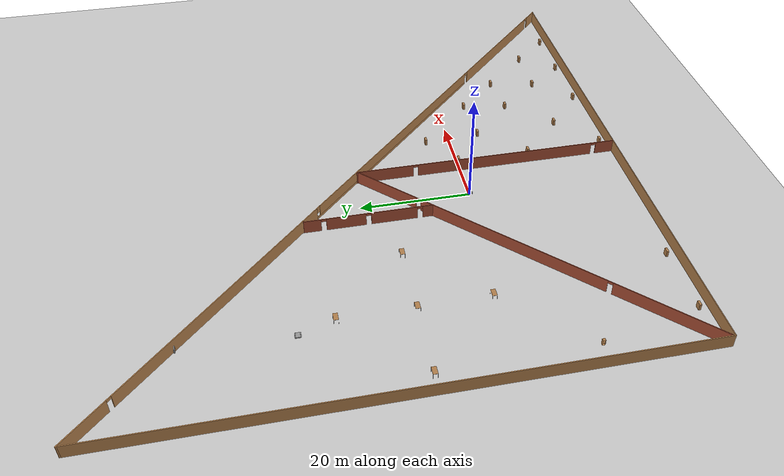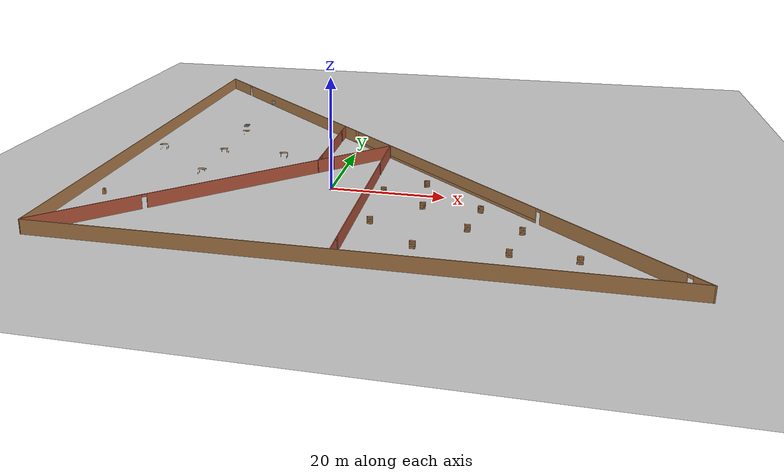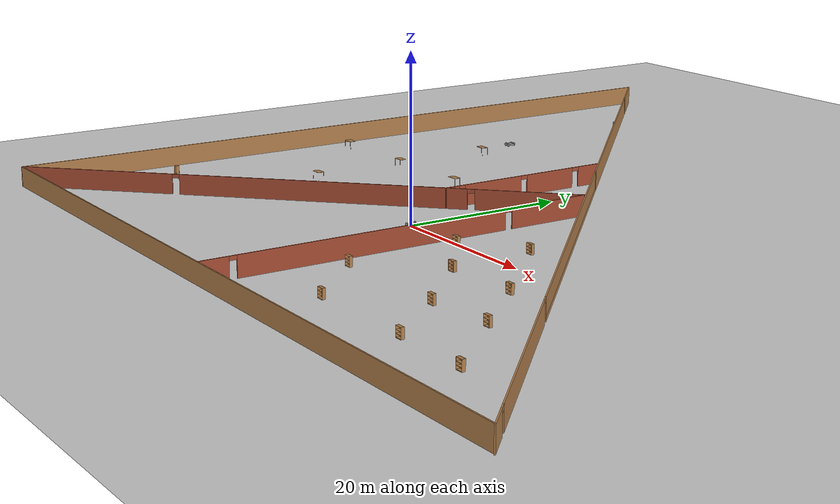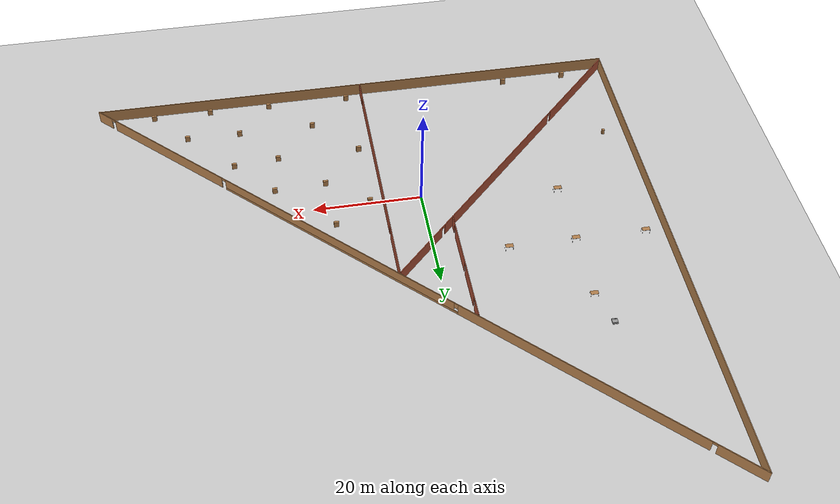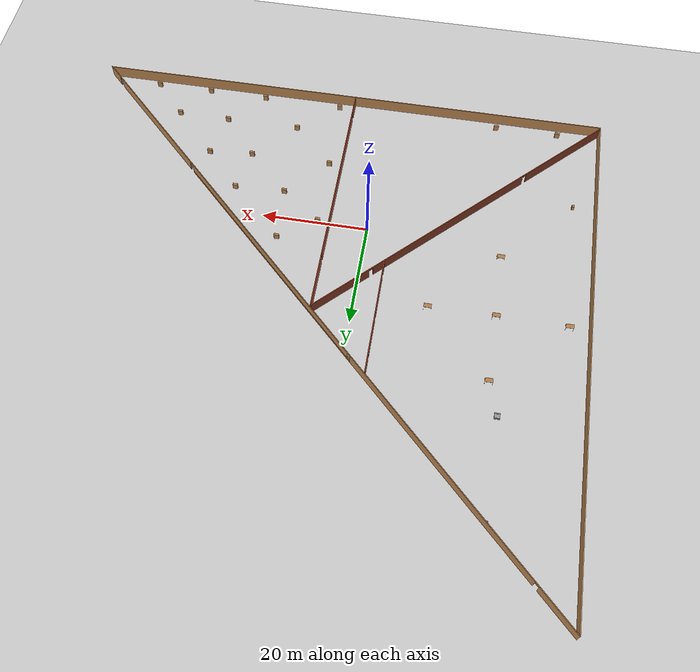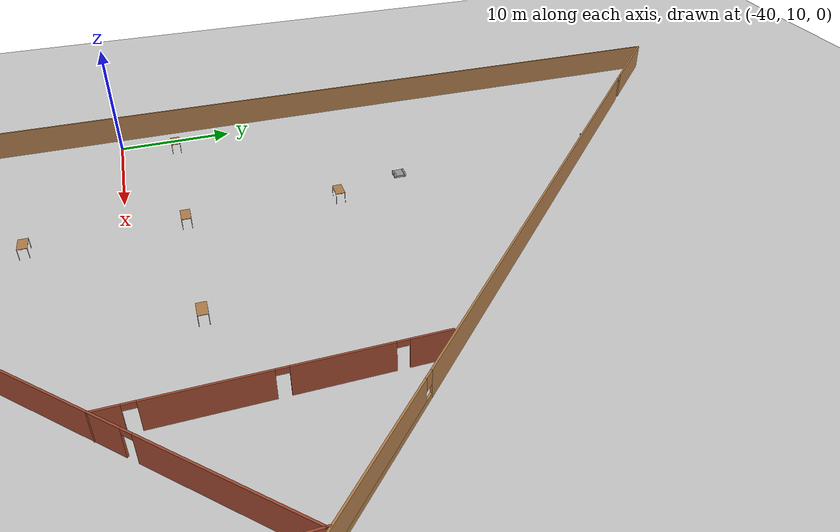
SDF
<sdf version="1.6">
 <world name="default">
  <plugin name="hello" filename="libhello.so"/>
  <light name="sun" type="directional">
   <pose>0 0 10 0 -0 0</pose>
   <diffuse>0.8 0.8 0.8 1</diffuse>
   <specular>0.1 0.1 0.1 1</specular>
   <attenuation>
    <range>1000</range>
    <constant>0.9</constant>
    <linear>0.01</linear>
    <quadratic>0.001</quadratic>
   </attenuation>
   <direction>-0.5 0.5 -1</direction>
  </light>
  <model name="ground_plane">
   <static>1</static>
   <link name="link">
    <collision name="collision">
     <geometry><plane><normal>0 0 1</normal><size>100 100</size></plane></geometry>
     <surface><friction><ode><mu>100</mu><mu2>50</mu2></ode></friction></surface>
    </collision>
    <visual name="visual">
     <cast_shadows>0</cast_shadows>
     <geometry><plane><normal>0 0 1</normal><size>100 100</size></plane></geometry>
     <material>
      <script><uri>file://media/materials/scripts/gazebo.material</uri><name>Gazebo/Grey</name></script>
     </material>
    </visual>
   </link>
  </model>
  <gravity>0 0 -9.8</gravity>
  <magnetic_field>6e-06 2.3e-05 -4.2e-05</magnetic_field>
  <atmosphere type="adiabatic"/>
  <physics name="default_physics" default="0" type="ode">
   <max_step_size>0.001</max_step_size>
   <real_time_factor>1</real_time_factor>
   <real_time_update_rate>1000</real_time_update_rate>
  </physics>
  <scene><ambient>0.4 0.4 0.4 1</ambient><background>0.7 0.7 0.7 1</background><shadows>1</shadows></scene>
  <spherical_coordinates>
   <surface_model>EARTH_WGS84</surface_model>
   <latitude_deg>0</latitude_deg>
   <longitude_deg>0</longitude_deg>
   <elevation>0</elevation>
   <heading_deg>0</heading_deg>
  </spherical_coordinates>
  <model name="robot">
   <link name="link_0">
    <inertial>
     <mass>0.118489</mass>
     <inertia>
      <ixx>0.00517304</ixx>
      <ixy>0</ixy>
      <ixz>0</ixz>
      <iyy>0.0128061</iyy>
      <iyz>0</iyz>
      <izz>0.0175459</izz>
     </inertia>
    </inertial>
    <visual name="visual">
     <geometry><box><size>0.3 1 0.1</size></box></geometry>
     <material>
      <lighting>1</lighting>
      <script><uri>file://media/materials/scripts/gazebo.material</uri><name>Gazebo/Grey</name></script>
      <ambient>0.3 0.3 0.3 1</ambient>
      <diffuse>0.7 0.7 0.7 1</diffuse>
      <specular>0.01 0.01 0.01 1</specular>
      <emissive>0 0 0 1</emissive>
      <shader type="vertex"><normal_map>__default__</normal_map></shader>
     </material>
    </visual>
    <visual name="ModelPreview_0::link_0::visual_1">
     <geometry><box><size>0.3 1 0.148101</size></box></geometry>
     <material>
      <lighting>1</lighting>
      <script><uri>file://media/materials/scripts/gazebo.material</uri><name>Gazebo/Grey</name></script>
      <ambient>0.3 0.3 0.3 1</ambient>
      <diffuse>0.7 0.7 0.7 1</diffuse>
      <specular>0.01 0.01 0.01 1</specular>
      <emissive>0 0 0 1</emissive>
      <shader type="vertex"><normal_map>__default__</normal_map></shader>
     </material>
    </visual>
    <collision name="collision">
     <geometry><box><size>0.3 1 0.1</size></box></geometry>
     <surface>
      <friction>
       <ode><mu>1</mu><mu2>1</mu2><fdir1>0 0 0</fdir1><slip1>0</slip1><slip2>0</slip2></ode>
       <torsional>
        <coefficient>1</coefficient>
        <patch_radius>0</patch_radius>
        <surface_radius>0</surface_radius>
        <use_patch_radius>1</use_patch_radius>
        <ode><slip>0</slip></ode>
       </torsional>
      </friction>
      <bounce><restitution_coefficient>0</restitution_coefficient><threshold>1e+06</threshold></bounce>
      <contact>
       <collide_without_contact>0</collide_without_contact>
       <collide_without_contact_bitmask>1</collide_without_contact_bitmask>
       <collide_bitmask>1</collide_bitmask>
       <ode>
        <soft_cfm>0</soft_cfm>
        <soft_erp>0.2</soft_erp>
        <kp>1e+13</kp>
        <kd>1</kd>
        <max_vel>0.01</max_vel>
        <min_depth>0</min_depth>
       </ode>
       <bullet>
        <split_impulse>1</split_impulse>
        <split_impulse_penetration_threshold>-0.01</split_impulse_penetration_threshold>
        <soft_cfm>0</soft_cfm>
        <soft_erp>0.2</soft_erp>
        <kp>1e+13</kp>
        <kd>1</kd>
       </bullet>
      </contact>
     </surface>
    </collision>
   </link>
   <link name="link_1">
    <pose>0 -0.542501 0 1.5708 -0 0</pose>
    <inertial>
     <mass>0.0996712</mass>
     <inertia>
      <ixx>0.00631196</ixx>
      <ixy>0</ixy>
      <ixz>0</ixz>
      <iyy>0.00631196</iyy>
      <iyz>0</iyz>
      <izz>0.0124589</izz>
     </inertia>
    </inertial>
    <visual name="visual">
     <geometry><cylinder><radius>0.25</radius><length>0.085</length></cylinder></geometry>
     <material>
      <lighting>1</lighting>
      <script><uri>file://media/materials/scripts/gazebo.material</uri><name>Gazebo/Grey</name></script>
      <ambient>0.3 0.3 0.3 1</ambient>
      <diffuse>0.7 0.7 0.7 1</diffuse>
      <specular>0.01 0.01 0.01 1</specular>
      <emissive>0 0 0 1</emissive>
      <shader type="vertex"><normal_map>__default__</normal_map></shader>
     </material>
    </visual>
    <collision name="collision">
     <geometry><cylinder><radius>0.25</radius><length>0.085</length></cylinder></geometry>
     <surface>
      <friction>
       <ode><mu>1</mu><mu2>1</mu2><fdir1>0 0 0</fdir1><slip1>0</slip1><slip2>0</slip2></ode>
       <torsional>
        <coefficient>1</coefficient>
        <patch_radius>0</patch_radius>
        <surface_radius>0</surface_radius>
        <use_patch_radius>1</use_patch_radius>
        <ode><slip>0</slip></ode>
       </torsional>
      </friction>
      <bounce><restitution_coefficient>0</restitution_coefficient><threshold>1e+06</threshold></bounce>
      <contact>
       <collide_without_contact>0</collide_without_contact>
       <collide_without_contact_bitmask>1</collide_without_contact_bitmask>
       <collide_bitmask>1</collide_bitmask>
       <ode>
        <soft_cfm>0</soft_cfm>
        <soft_erp>0.2</soft_erp>
        <kp>1e+13</kp>
        <kd>1</kd>
        <max_vel>0.01</max_vel>
        <min_depth>0</min_depth>
       </ode>
       <bullet>
        <split_impulse>1</split_impulse>
        <split_impulse_penetration_threshold>-0.01</split_impulse_penetration_threshold>
        <soft_cfm>0</soft_cfm>
        <soft_erp>0.2</soft_erp>
        <kp>1e+13</kp>
        <kd>1</kd>
       </bullet>
      </contact>
     </surface>
    </collision>
   </link>
   <link name="link_1_clone">
    <pose>0 0.542501 0 1.5708 -0 0</pose>
    <inertial>
     <mass>0.0996712</mass>
     <inertia>
      <ixx>0.00631196</ixx>
      <ixy>0</ixy>
      <ixz>0</ixz>
      <iyy>0.00631196</iyy>
      <iyz>0</iyz>
      <izz>0.0124589</izz>
     </inertia>
    </inertial>
    <visual name="visual">
     <geometry><cylinder><radius>0.25</radius><length>0.085</length></cylinder></geometry>
     <material>
      <lighting>1</lighting>
      <script><uri>file://media/materials/scripts/gazebo.material</uri><name>Gazebo/Grey</name></script>
      <ambient>0.3 0.3 0.3 1</ambient>
      <diffuse>0.7 0.7 0.7 1</diffuse>
      <specular>0.01 0.01 0.01 1</specular>
      <emissive>0 0 0 1</emissive>
      <shader type="vertex"><normal_map>__default__</normal_map></shader>
     </material>
    </visual>
    <collision name="collision">
     <geometry><cylinder><radius>0.25</radius><length>0.085</length></cylinder></geometry>
     <surface>
      <friction>
       <ode><mu>1</mu><mu2>1</mu2><fdir1>0 0 0</fdir1><slip1>0</slip1><slip2>0</slip2></ode>
       <torsional>
        <coefficient>1</coefficient>
        <patch_radius>0</patch_radius>
        <surface_radius>0</surface_radius>
        <use_patch_radius>1</use_patch_radius>
        <ode><slip>0</slip></ode>
       </torsional>
      </friction>
      <bounce><restitution_coefficient>0</restitution_coefficient><threshold>1e+06</threshold></bounce>
      <contact>
       <collide_without_contact>0</collide_without_contact>
       <collide_without_contact_bitmask>1</collide_without_contact_bitmask>
       <collide_bitmask>1</collide_bitmask>
       <ode>
        <soft_cfm>0</soft_cfm>
        <soft_erp>0.2</soft_erp>
        <kp>1e+13</kp>
        <kd>1</kd>
        <max_vel>0.01</max_vel>
        <min_depth>0</min_depth>
       </ode>
       <bullet>
        <split_impulse>1</split_impulse>
        <split_impulse_penetration_threshold>-0.01</split_impulse_penetration_threshold>
        <soft_cfm>0</soft_cfm>
        <soft_erp>0.2</soft_erp>
        <kp>1e+13</kp>
        <kd>1</kd>
       </bullet>
      </contact>
     </surface>
    </collision>
   </link>
   <joint name="link_0_JOINT_0" type="revolute">
    <parent>link_0</parent>
    <child>link_1</child>
    <axis>
     <xyz>0 0 1</xyz>
     <use_parent_model_frame>0</use_parent_model_frame>
     <limit>
      <lower>-1.79769e+308</lower>
      <upper>1.79769e+308</upper>
      <effort>-1</effort>
      <velocity>-1</velocity>
     </limit>
     <dynamics>
      <spring_reference>0</spring_reference>
      <spring_stiffness>0</spring_stiffness>
      <damping>0</damping>
     </dynamics>
    </axis>
    <physics>
     <ode><limit><cfm>0</cfm><erp>0.2</erp></limit><suspension><cfm>0</cfm><erp>0.2</erp></suspension></ode>
    </physics>
   </joint>
   <joint name="link_0_JOINT_1" type="revolute">
    <parent>link_0</parent>
    <child>link_1_clone</child>
    <axis>
     <xyz>0 0 1</xyz>
     <use_parent_model_frame>0</use_parent_model_frame>
     <limit>
      <lower>-1.79769e+308</lower>
      <upper>1.79769e+308</upper>
      <effort>-1</effort>
      <velocity>-1</velocity>
     </limit>
     <dynamics>
      <spring_reference>0</spring_reference>
      <spring_stiffness>0</spring_stiffness>
      <damping>0</damping>
     </dynamics>
    </axis>
    <physics>
     <ode><limit><cfm>0</cfm><erp>0.2</erp></limit><suspension><cfm>0</cfm><erp>0.2</erp></suspension></ode>
    </physics>
   </joint>
   <static>0</static>
   <pose>0 -0.002691 0.25 0 -0 0</pose>
  </model>
  <model name="Building">
   <pose>8.1557 18.4087 0 0 -0 0</pose>
   <link name="Wall_1">
    <collision name="Wall_1_Collision">
     <geometry><box><size>96.8752 0.15 2.5</size></box></geometry>
     <pose>0 0 1.25 0 -0 0</pose>
    </collision>
    <visual name="Wall_1_Visual">
     <pose>0 0 1.25 0 -0 0</pose>
     <geometry><box><size>96.8752 0.15 2.5</size></box></geometry>
     <material>
      <script><uri>file://media/materials/scripts/gazebo.material</uri><name>Gazebo/Wood</name></script>
      <ambient>1 0.764706 0.305882 1</ambient>
     </material>
    </visual>
    <pose>-49.9405 -0.078415 0 0 -0 1.56903</pose>
   </link>
   <link name="Wall_15">
    <pose>-25.4387 -23.6088 0 0 -0 0.785398</pose>
    <visual name="Wall_15_Visual_0">
     <pose>-25.0598 0 1.25 0 -0 0</pose>
     <geometry><box><size>19.1305 0.15 2.5</size></box></geometry>
     <material>
      <script><uri>file://media/materials/scripts/gazebo.material</uri><name>Gazebo/Bricks</name></script>
      <ambient>1 1 1 1</ambient>
     </material>
    </visual>
    <collision name="Wall_15_Collision_0">
     <geometry><box><size>19.1305 0.15 2.5</size></box></geometry>
     <pose>-25.0598 0 1.25 0 -0 0</pose>
    </collision>
    <visual name="Wall_15_Visual_1">
     <pose>3.11936 0 1.25 0 -0 0</pose>
     <geometry><box><size>35.4277 0.15 2.5</size></box></geometry>
     <material>
      <script><uri>file://media/materials/scripts/gazebo.material</uri><name>Gazebo/Bricks</name></script>
      <ambient>1 1 1 1</ambient>
     </material>
    </visual>
    <collision name="Wall_15_Collision_1">
     <geometry><box><size>35.4277 0.15 2.5</size></box></geometry>
     <pose>3.11936 0 1.25 0 -0 0</pose>
    </collision>
    <visual name="Wall_15_Visual_2">
     <pose>28.1791 0 1.25 0 -0 0</pose>
     <geometry><box><size>12.8918 0.15 2.5</size></box></geometry>
     <material>
      <script><uri>file://media/materials/scripts/gazebo.material</uri><name>Gazebo/Bricks</name></script>
      <ambient>1 1 1 1</ambient>
     </material>
    </visual>
    <collision name="Wall_15_Collision_2">
     <geometry><box><size>12.8918 0.15 2.5</size></box></geometry>
     <pose>28.1791 0 1.25 0 -0 0</pose>
    </collision>
    <visual name="Wall_15_Visual_3">
     <pose>-15.0445 0 2.25 0 -0 0</pose>
     <geometry><box><size>0.9 0.15 0.5</size></box></geometry>
     <material>
      <script><uri>file://media/materials/scripts/gazebo.material</uri><name>Gazebo/Bricks</name></script>
      <ambient>1 1 1 1</ambient>
     </material>
    </visual>
    <collision name="Wall_15_Collision_3">
     <geometry><box><size>0.9 0.15 0.5</size></box></geometry>
     <pose>-15.0445 0 2.25 0 -0 0</pose>
    </collision>
    <visual name="Wall_15_Visual_4">
     <pose>21.2832 0 2.25 0 -0 0</pose>
     <geometry><box><size>0.9 0.15 0.5</size></box></geometry>
     <material>
      <script><uri>file://media/materials/scripts/gazebo.material</uri><name>Gazebo/Bricks</name></script>
      <ambient>1 1 1 1</ambient>
     </material>
    </visual>
    <collision name="Wall_15_Collision_4">
     <geometry><box><size>0.9 0.15 0.5</size></box></geometry>
     <pose>21.2832 0 2.25 0 -0 0</pose>
    </collision>
   </link>
   <link name="Wall_17">
    <pose>-1.03505 -23.7009 0 0 0 -1.5708</pose>
    <visual name="Wall_17_Visual_0">
     <pose>-19.4576 0 1.25 0 -0 0</pose>
     <geometry><box><size>10.5847 0.15 2.5</size></box></geometry>
     <material>
      <script><uri>file://media/materials/scripts/gazebo.material</uri><name>Gazebo/Bricks</name></script>
      <ambient>1 1 1 1</ambient>
     </material>
    </visual>
    <collision name="Wall_17_Collision_0">
     <geometry><box><size>10.5847 0.15 2.5</size></box></geometry>
     <pose>-19.4576 0 1.25 0 -0 0</pose>
    </collision>
    <visual name="Wall_17_Visual_1">
     <pose>3.52788 0 1.25 0 -0 0</pose>
     <geometry><box><size>33.5863 0.15 2.5</size></box></geometry>
     <material>
      <script><uri>file://media/materials/scripts/gazebo.material</uri><name>Gazebo/Bricks</name></script>
      <ambient>1 1 1 1</ambient>
     </material>
    </visual>
    <collision name="Wall_17_Collision_1">
     <geometry><box><size>33.5863 0.15 2.5</size></box></geometry>
     <pose>3.52788 0 1.25 0 -0 0</pose>
    </collision>
    <visual name="Wall_17_Visual_2">
     <pose>22.9855 0 1.25 0 -0 0</pose>
     <geometry><box><size>3.52897 0.15 2.5</size></box></geometry>
     <material>
      <script><uri>file://media/materials/scripts/gazebo.material</uri><name>Gazebo/Bricks</name></script>
      <ambient>1 1 1 1</ambient>
     </material>
    </visual>
    <collision name="Wall_17_Collision_2">
     <geometry><box><size>3.52897 0.15 2.5</size></box></geometry>
     <pose>22.9855 0 1.25 0 -0 0</pose>
    </collision>
    <visual name="Wall_17_Visual_3">
     <pose>-13.7153 0 2.25 0 -0 0</pose>
     <geometry><box><size>0.9 0.15 0.5</size></box></geometry>
     <material>
      <script><uri>file://media/materials/scripts/gazebo.material</uri><name>Gazebo/Bricks</name></script>
      <ambient>1 1 1 1</ambient>
     </material>
    </visual>
    <collision name="Wall_17_Collision_3">
     <geometry><box><size>0.9 0.15 0.5</size></box></geometry>
     <pose>-13.7153 0 2.25 0 -0 0</pose>
    </collision>
    <visual name="Wall_17_Visual_4">
     <pose>20.771 0 2.25 0 -0 0</pose>
     <geometry><box><size>0.9 0.15 0.5</size></box></geometry>
     <material>
      <script><uri>file://media/materials/scripts/gazebo.material</uri><name>Gazebo/Bricks</name></script>
      <ambient>1 1 1 1</ambient>
     </material>
    </visual>
    <collision name="Wall_17_Collision_4">
     <geometry><box><size>0.9 0.15 0.5</size></box></geometry>
     <pose>20.771 0 2.25 0 -0 0</pose>
    </collision>
   </link>
   <link name="Wall_3">
    <pose>0.069793 1e-06 0 0 0 -0.771261</pose>
    <visual name="Wall_3_Visual_0">
     <pose>-65.3239 0 1.25 0 -0 0</pose>
     <geometry><box><size>8.75684 0.15 2.5</size></box></geometry>
     <material>
      <script><uri>file://media/materials/scripts/gazebo.material</uri><name>Gazebo/Wood</name></script>
      <ambient>1 0.764706 0.305882 1</ambient>
     </material>
    </visual>
    <collision name="Wall_3_Collision_0">
     <geometry><box><size>8.75684 0.15 2.5</size></box></geometry>
     <pose>-65.3239 0 1.25 0 -0 0</pose>
    </collision>
    <visual name="Wall_3_Visual_1">
     <pose>-36.7119 0 1.25 0 -0 0</pose>
     <geometry><box><size>46.6672 0.15 2.5</size></box></geometry>
     <material>
      <script><uri>file://media/materials/scripts/gazebo.material</uri><name>Gazebo/Wood</name></script>
      <ambient>1 0.764706 0.305882 1</ambient>
     </material>
    </visual>
    <collision name="Wall_3_Collision_1">
     <geometry><box><size>46.6672 0.15 2.5</size></box></geometry>
     <pose>-36.7119 0 1.25 0 -0 0</pose>
    </collision>
    <visual name="Wall_3_Visual_2">
     <pose>51.9944 0 1.25 0 -0 0</pose>
     <geometry><box><size>26.7455 0.15 2.5</size></box></geometry>
     <material>
      <script><uri>file://media/materials/scripts/gazebo.material</uri><name>Gazebo/Wood</name></script>
      <ambient>1 0.764706 0.305882 1</ambient>
     </material>
    </visual>
    <collision name="Wall_3_Collision_2">
     <geometry><box><size>26.7455 0.15 2.5</size></box></geometry>
     <pose>51.9944 0 1.25 0 -0 0</pose>
    </collision>
    <visual name="Wall_3_Visual_3">
     <pose>67.9847 0 1.25 0 -0 0</pose>
     <geometry><box><size>3.43514 0.15 2.5</size></box></geometry>
     <material>
      <script><uri>file://media/materials/scripts/gazebo.material</uri><name>Gazebo/Wood</name></script>
      <ambient>1 0.764706 0.305882 1</ambient>
     </material>
    </visual>
    <collision name="Wall_3_Collision_3">
     <geometry><box><size>3.43514 0.15 2.5</size></box></geometry>
     <pose>67.9847 0 1.25 0 -0 0</pose>
    </collision>
    <visual name="Wall_3_Visual_4">
     <pose>12.1717 0 0.25 0 -0 0</pose>
     <geometry><box><size>51.0999 0.15 0.5</size></box></geometry>
     <material>
      <script><uri>file://media/materials/scripts/gazebo.material</uri><name>Gazebo/Wood</name></script>
      <ambient>1 0.764706 0.305882 1</ambient>
     </material>
    </visual>
    <collision name="Wall_3_Collision_4">
     <geometry><box><size>51.0999 0.15 0.5</size></box></geometry>
     <pose>12.1717 0 0.25 0 -0 0</pose>
    </collision>
    <visual name="Wall_3_Visual_5">
     <pose>12.5717 0 1.5 0 -0 0</pose>
     <geometry><box><size>50.2999 0.15 2</size></box></geometry>
     <material>
      <script><uri>file://media/materials/scripts/gazebo.material</uri><name>Gazebo/Wood</name></script>
      <ambient>1 0.764706 0.305882 1</ambient>
     </material>
    </visual>
    <collision name="Wall_3_Collision_5">
     <geometry><box><size>50.2999 0.15 2</size></box></geometry>
     <pose>12.5717 0 1.5 0 -0 0</pose>
    </collision>
    <visual name="Wall_3_Visual_6">
     <pose>-12.9783 0 1.9 0 -0 0</pose>
     <geometry><box><size>0.8 0.15 1.2</size></box></geometry>
     <material>
      <script><uri>file://media/materials/scripts/gazebo.material</uri><name>Gazebo/Wood</name></script>
      <ambient>1 0.764706 0.305882 1</ambient>
     </material>
    </visual>
    <collision name="Wall_3_Collision_6">
     <geometry><box><size>0.8 0.15 1.2</size></box></geometry>
     <pose>-12.9783 0 1.9 0 -0 0</pose>
    </collision>
    <visual name="Wall_3_Visual_7">
     <pose>-60.4954 0 2.25 0 -0 0</pose>
     <geometry><box><size>0.9 0.15 0.5</size></box></geometry>
     <material>
      <script><uri>file://media/materials/scripts/gazebo.material</uri><name>Gazebo/Wood</name></script>
      <ambient>1 0.764706 0.305882 1</ambient>
     </material>
    </visual>
    <collision name="Wall_3_Collision_7">
     <geometry><box><size>0.9 0.15 0.5</size></box></geometry>
     <pose>-60.4954 0 2.25 0 -0 0</pose>
    </collision>
    <visual name="Wall_3_Visual_8">
     <pose>65.8171 0 2.25 0 -0 0</pose>
     <geometry><box><size>0.9 0.15 0.5</size></box></geometry>
     <material>
      <script><uri>file://media/materials/scripts/gazebo.material</uri><name>Gazebo/Wood</name></script>
      <ambient>1 0.764706 0.305882 1</ambient>
     </material>
    </visual>
    <collision name="Wall_3_Collision_8">
     <geometry><box><size>0.9 0.15 0.5</size></box></geometry>
     <pose>65.8171 0 2.25 0 -0 0</pose>
    </collision>
    <visual name="Wall_3_Visual_9">
     <pose>38.1716 0 2.25 0 -0 0</pose>
     <geometry><box><size>0.9 0.15 0.5</size></box></geometry>
     <material>
      <script><uri>file://media/materials/scripts/gazebo.material</uri><name>Gazebo/Wood</name></script>
      <ambient>1 0.764706 0.305882 1</ambient>
     </material>
    </visual>
    <collision name="Wall_3_Collision_9">
     <geometry><box><size>0.9 0.15 0.5</size></box></geometry>
     <pose>38.1716 0 2.25 0 -0 0</pose>
    </collision>
   </link>
   <link name="Wall_5">
    <collision name="Wall_5_Collision">
     <geometry><box><size>100 0.15 2.5</size></box></geometry>
     <pose>0 0 1.25 0 -0 0</pose>
    </collision>
    <visual name="Wall_5_Visual">
     <pose>0 0 1.25 0 -0 0</pose>
     <geometry><box><size>100 0.15 2.5</size></box></geometry>
     <material>
      <script><uri>file://media/materials/scripts/gazebo.material</uri><name>Gazebo/Wood</name></script>
      <ambient>1 0.764706 0.305882 1</ambient>
     </material>
    </visual>
    <pose>-0.100561 -48.4411 0 0 0 -4e-06</pose>
   </link>
   <link name="Window_1">
    <collision name="Window_1_Collision">
     <geometry><box><size>0.8 0.17 0.8</size></box></geometry>
     <pose>0 0 0.4 0 -0 0</pose>
    </collision>
    <visual name="Window_1_Visual">
     <pose>0 0 0.4 0 -0 0</pose>
     <geometry><box><size>0.8 0.17 0.8</size></box></geometry>
     <material>
      <script><uri>file://media/materials/scripts/gazebo.material</uri><name>Gazebo/Grey</name></script>
     </material>
    </visual>
    <pose>-34.9574 33.5803 0.5 0 -0 0</pose>
   </link>
   <static>1</static>
  </model>
  <model name="cabinet">
   <static>1</static>
   <link name="cabinet_bottom_plate">
    <inertial>
     <pose>0 0 -1 0 -0 0</pose>
     <inertia><ixx>2.05</ixx><ixy>0</ixy><ixz>0</ixz><iyy>2.05</iyy><iyz>0</iyz><izz>2.05</izz></inertia>
     <mass>25</mass>
    </inertial>
    <collision name="cabinet_bottom_plate_geom">
     <pose>0 0 0.01 0 -0 0</pose>
     <geometry><box><size>0.45 0.45 0.02</size></box></geometry>
    </collision>
    <visual name="cabinet_bottom_plate_geom_visual">
     <pose>0 0 0.01 0 -0 0</pose>
     <geometry><box><size>0.45 0.45 0.02</size></box></geometry>
     <material>
      <script><uri>file://media/materials/scripts/gazebo.material</uri><name>Gazebo/Wood</name></script>
     </material>
    </visual>
    <collision name="cabinet_bottom_plate_geom_cabinet_back_plate">
     <pose>0.235 0 0.51 0 -0 0</pose>
     <geometry><box><size>0.02 0.45 1.02</size></box></geometry>
    </collision>
    <visual name="cabinet_bottom_plate_geom_cabinet_back_plate_visual">
     <pose>0.235 0 0.51 0 -0 0</pose>
     <geometry><box><size>0.02 0.45 1.02</size></box></geometry>
     <material>
      <script><uri>file://media/materials/scripts/gazebo.material</uri><name>Gazebo/Wood</name></script>
     </material>
    </visual>
    <collision name="cabinet_bottom_plate_geom_cabinet_left_plate">
     <pose>0 0.235 0.51 0 -0 0</pose>
     <geometry><box><size>0.45 0.02 1.02</size></box></geometry>
    </collision>
    <visual name="cabinet_bottom_plate_geom_cabinet_left_plate_visual">
     <pose>0 0.235 0.51 0 -0 0</pose>
     <geometry><box><size>0.45 0.02 1.02</size></box></geometry>
     <material>
      <script><uri>file://media/materials/scripts/gazebo.material</uri><name>Gazebo/Wood</name></script>
     </material>
    </visual>
    <collision name="cabinet_bottom_plate_geom_cabinet_middle_plate">
     <pose>0 0 0.51 0 -0 0</pose>
     <geometry><box><size>0.45 0.45 0.02</size></box></geometry>
    </collision>
    <visual name="cabinet_bottom_plate_geom_cabinet_middle_plate_visual">
     <pose>0 0 0.51 0 -0 0</pose>
     <geometry><box><size>0.45 0.45 0.02</size></box></geometry>
     <material>
      <script><uri>file://media/materials/scripts/gazebo.material</uri><name>Gazebo/Wood</name></script>
     </material>
    </visual>
    <collision name="cabinet_bottom_plate_geom_cabinet_right_plate">
     <pose>0 -0.235 0.51 0 -0 0</pose>
     <geometry><box><size>0.45 0.02 1.02</size></box></geometry>
    </collision>
    <visual name="cabinet_bottom_plate_geom_cabinet_right_plate_visual">
     <pose>0 -0.235 0.51 0 -0 0</pose>
     <geometry><box><size>0.45 0.02 1.02</size></box></geometry>
     <material>
      <script><uri>file://media/materials/scripts/gazebo.material</uri><name>Gazebo/Wood</name></script>
     </material>
    </visual>
    <collision name="cabinet_bottom_plate_geom_cabinet_top_plate">
     <pose>0 0 1.01 0 -0 0</pose>
     <geometry><box><size>0.45 0.45 0.02</size></box></geometry>
    </collision>
    <visual name="cabinet_bottom_plate_geom_cabinet_top_plate_visual">
     <pose>0 0 1.01 0 -0 0</pose>
     <geometry><box><size>0.45 0.45 0.02</size></box></geometry>
     <material>
      <script><uri>file://media/materials/scripts/gazebo.material</uri><name>Gazebo/Wood</name></script>
     </material>
    </visual>
   </link>
   <pose>-37.689 -11.175 0 0 -0 0</pose>
  </model>
  <model name="bookshelf">
   <static>1</static>
   <link name="link">
    <inertial><mass>1</mass></inertial>
    <collision name="back">
     <pose>0 0.005 0.6 0 -0 0</pose>
     <geometry><box><size>0.9 0.01 1.2</size></box></geometry>
    </collision>
    <visual name="visual1">
     <pose>0 0.005 0.6 0 -0 0</pose>
     <geometry><box><size>0.9 0.01 1.2</size></box></geometry>
     <material>
      <script><uri>file://media/materials/scripts/gazebo.material</uri><name>Gazebo/Wood</name></script>
     </material>
    </visual>
    <collision name="left_side">
     <pose>0.45 -0.195 0.6 0 -0 0</pose>
     <geometry><box><size>0.02 0.4 1.2</size></box></geometry>
    </collision>
    <visual name="visual2">
     <pose>0.45 -0.195 0.6 0 -0 0</pose>
     <geometry><box><size>0.02 0.4 1.2</size></box></geometry>
     <material>
      <script><uri>file://media/materials/scripts/gazebo.material</uri><name>Gazebo/Wood</name></script>
     </material>
    </visual>
    <collision name="right_side">
     <pose>-0.45 -0.195 0.6 0 -0 0</pose>
     <geometry><box><size>0.02 0.4 1.2</size></box></geometry>
    </collision>
    <visual name="visual3">
     <pose>-0.45 -0.195 0.6 0 -0 0</pose>
     <geometry><box><size>0.02 0.4 1.2</size></box></geometry>
     <material>
      <script><uri>file://media/materials/scripts/gazebo.material</uri><name>Gazebo/Wood</name></script>
     </material>
    </visual>
    <collision name="bottom">
     <pose>0 -0.195 0.03 0 -0 0</pose>
     <geometry><box><size>0.88 0.4 0.06</size></box></geometry>
    </collision>
    <visual name="visual4">
     <pose>0 -0.195 0.03 0 -0 0</pose>
     <geometry><box><size>0.88 0.4 0.06</size></box></geometry>
     <material>
      <script><uri>file://media/materials/scripts/gazebo.material</uri><name>Gazebo/Wood</name></script>
     </material>
    </visual>
    <collision name="top">
     <pose>0 -0.195 1.19 0 -0 0</pose>
     <geometry><box><size>0.88 0.4 0.02</size></box></geometry>
    </collision>
    <visual name="visual5">
     <pose>0 -0.195 1.19 0 -0 0</pose>
     <geometry><box><size>0.88 0.4 0.02</size></box></geometry>
     <material>
      <script><uri>file://media/materials/scripts/gazebo.material</uri><name>Gazebo/Wood</name></script>
     </material>
    </visual>
    <collision name="low_shelf">
     <pose>0 -0.195 0.43 0 -0 0</pose>
     <geometry><box><size>0.88 0.4 0.02</size></box></geometry>
    </collision>
    <visual name="visual6">
     <pose>0 -0.195 0.43 0 -0 0</pose>
     <geometry><box><size>0.88 0.4 0.02</size></box></geometry>
     <material>
      <script><uri>file://media/materials/scripts/gazebo.material</uri><name>Gazebo/Wood</name></script>
     </material>
    </visual>
    <collision name="high_shelf">
     <pose>0 -0.195 0.8 0 -0 0</pose>
     <geometry><box><size>0.88 0.4 0.02</size></box></geometry>
    </collision>
    <visual name="visual7">
     <pose>0 -0.195 0.8 0 -0 0</pose>
     <geometry><box><size>0.88 0.4 0.02</size></box></geometry>
     <material>
      <script><uri>file://media/materials/scripts/gazebo.material</uri><name>Gazebo/Wood</name></script>
     </material>
    </visual>
   </link>
   <pose>10.1187 -28.3726 0 0 -0 0</pose>
  </model>
  <model name="bookshelf_clone">
   <static>1</static>
   <link name="link">
    <inertial><mass>1</mass></inertial>
    <collision name="back">
     <pose>0 0.005 0.6 0 -0 0</pose>
     <geometry><box><size>0.9 0.01 1.2</size></box></geometry>
    </collision>
    <visual name="visual1">
     <pose>0 0.005 0.6 0 -0 0</pose>
     <geometry><box><size>0.9 0.01 1.2</size></box></geometry>
     <material>
      <script><uri>file://media/materials/scripts/gazebo.material</uri><name>Gazebo/Wood</name></script>
     </material>
    </visual>
    <collision name="left_side">
     <pose>0.45 -0.195 0.6 0 -0 0</pose>
     <geometry><box><size>0.02 0.4 1.2</size></box></geometry>
    </collision>
    <visual name="visual2">
     <pose>0.45 -0.195 0.6 0 -0 0</pose>
     <geometry><box><size>0.02 0.4 1.2</size></box></geometry>
     <material>
      <script><uri>file://media/materials/scripts/gazebo.material</uri><name>Gazebo/Wood</name></script>
     </material>
    </visual>
    <collision name="right_side">
     <pose>-0.45 -0.195 0.6 0 -0 0</pose>
     <geometry><box><size>0.02 0.4 1.2</size></box></geometry>
    </collision>
    <visual name="visual3">
     <pose>-0.45 -0.195 0.6 0 -0 0</pose>
     <geometry><box><size>0.02 0.4 1.2</size></box></geometry>
     <material>
      <script><uri>file://media/materials/scripts/gazebo.material</uri><name>Gazebo/Wood</name></script>
     </material>
    </visual>
    <collision name="bottom">
     <pose>0 -0.195 0.03 0 -0 0</pose>
     <geometry><box><size>0.88 0.4 0.06</size></box></geometry>
    </collision>
    <visual name="visual4">
     <pose>0 -0.195 0.03 0 -0 0</pose>
     <geometry><box><size>0.88 0.4 0.06</size></box></geometry>
     <material>
      <script><uri>file://media/materials/scripts/gazebo.material</uri><name>Gazebo/Wood</name></script>
     </material>
    </visual>
    <collision name="top">
     <pose>0 -0.195 1.19 0 -0 0</pose>
     <geometry><box><size>0.88 0.4 0.02</size></box></geometry>
    </collision>
    <visual name="visual5">
     <pose>0 -0.195 1.19 0 -0 0</pose>
     <geometry><box><size>0.88 0.4 0.02</size></box></geometry>
     <material>
      <script><uri>file://media/materials/scripts/gazebo.material</uri><name>Gazebo/Wood</name></script>
     </material>
    </visual>
    <collision name="low_shelf">
     <pose>0 -0.195 0.43 0 -0 0</pose>
     <geometry><box><size>0.88 0.4 0.02</size></box></geometry>
    </collision>
    <visual name="visual6">
     <pose>0 -0.195 0.43 0 -0 0</pose>
     <geometry><box><size>0.88 0.4 0.02</size></box></geometry>
     <material>
      <script><uri>file://media/materials/scripts/gazebo.material</uri><name>Gazebo/Wood</name></script>
     </material>
    </visual>
    <collision name="high_shelf">
     <pose>0 -0.195 0.8 0 -0 0</pose>
     <geometry><box><size>0.88 0.4 0.02</size></box></geometry>
    </collision>
    <visual name="visual7">
     <pose>0 -0.195 0.8 0 -0 0</pose>
     <geometry><box><size>0.88 0.4 0.02</size></box></geometry>
     <material>
      <script><uri>file://media/materials/scripts/gazebo.material</uri><name>Gazebo/Wood</name></script>
     </material>
    </visual>
   </link>
   <pose>36.9723 -28.5003 0 0 -0 0</pose>
  </model>
  <model name="bookshelf_clone_0">
   <static>1</static>
   <link name="link">
    <inertial><mass>1</mass></inertial>
    <collision name="back">
     <pose>0 0.005 0.6 0 -0 0</pose>
     <geometry><box><size>0.9 0.01 1.2</size></box></geometry>
    </collision>
    <visual name="visual1">
     <pose>0 0.005 0.6 0 -0 0</pose>
     <geometry><box><size>0.9 0.01 1.2</size></box></geometry>
     <material>
      <script><uri>file://media/materials/scripts/gazebo.material</uri><name>Gazebo/Wood</name></script>
     </material>
    </visual>
    <collision name="left_side">
     <pose>0.45 -0.195 0.6 0 -0 0</pose>
     <geometry><box><size>0.02 0.4 1.2</size></box></geometry>
    </collision>
    <visual name="visual2">
     <pose>0.45 -0.195 0.6 0 -0 0</pose>
     <geometry><box><size>0.02 0.4 1.2</size></box></geometry>
     <material>
      <script><uri>file://media/materials/scripts/gazebo.material</uri><name>Gazebo/Wood</name></script>
     </material>
    </visual>
    <collision name="right_side">
     <pose>-0.45 -0.195 0.6 0 -0 0</pose>
     <geometry><box><size>0.02 0.4 1.2</size></box></geometry>
    </collision>
    <visual name="visual3">
     <pose>-0.45 -0.195 0.6 0 -0 0</pose>
     <geometry><box><size>0.02 0.4 1.2</size></box></geometry>
     <material>
      <script><uri>file://media/materials/scripts/gazebo.material</uri><name>Gazebo/Wood</name></script>
     </material>
    </visual>
    <collision name="bottom">
     <pose>0 -0.195 0.03 0 -0 0</pose>
     <geometry><box><size>0.88 0.4 0.06</size></box></geometry>
    </collision>
    <visual name="visual4">
     <pose>0 -0.195 0.03 0 -0 0</pose>
     <geometry><box><size>0.88 0.4 0.06</size></box></geometry>
     <material>
      <script><uri>file://media/materials/scripts/gazebo.material</uri><name>Gazebo/Wood</name></script>
     </material>
    </visual>
    <collision name="top">
     <pose>0 -0.195 1.19 0 -0 0</pose>
     <geometry><box><size>0.88 0.4 0.02</size></box></geometry>
    </collision>
    <visual name="visual5">
     <pose>0 -0.195 1.19 0 -0 0</pose>
     <geometry><box><size>0.88 0.4 0.02</size></box></geometry>
     <material>
      <script><uri>file://media/materials/scripts/gazebo.material</uri><name>Gazebo/Wood</name></script>
     </material>
    </visual>
    <collision name="low_shelf">
     <pose>0 -0.195 0.43 0 -0 0</pose>
     <geometry><box><size>0.88 0.4 0.02</size></box></geometry>
    </collision>
    <visual name="visual6">
     <pose>0 -0.195 0.43 0 -0 0</pose>
     <geometry><box><size>0.88 0.4 0.02</size></box></geometry>
     <material>
      <script><uri>file://media/materials/scripts/gazebo.material</uri><name>Gazebo/Wood</name></script>
     </material>
    </visual>
    <collision name="high_shelf">
     <pose>0 -0.195 0.8 0 -0 0</pose>
     <geometry><box><size>0.88 0.4 0.02</size></box></geometry>
    </collision>
    <visual name="visual7">
     <pose>0 -0.195 0.8 0 -0 0</pose>
     <geometry><box><size>0.88 0.4 0.02</size></box></geometry>
     <material>
      <script><uri>file://media/materials/scripts/gazebo.material</uri><name>Gazebo/Wood</name></script>
     </material>
    </visual>
   </link>
   <pose>25.4694 -28.434 0 0 -0 0</pose>
  </model>
  <model name="bookshelf_clone_clone">
   <static>1</static>
   <link name="link">
    <inertial><mass>1</mass></inertial>
    <collision name="back">
     <pose>0 0.005 0.6 0 -0 0</pose>
     <geometry><box><size>0.9 0.01 1.2</size></box></geometry>
    </collision>
    <visual name="visual1">
     <pose>0 0.005 0.6 0 -0 0</pose>
     <geometry><box><size>0.9 0.01 1.2</size></box></geometry>
     <material>
      <script><uri>file://media/materials/scripts/gazebo.material</uri><name>Gazebo/Wood</name></script>
     </material>
    </visual>
    <collision name="left_side">
     <pose>0.45 -0.195 0.6 0 -0 0</pose>
     <geometry><box><size>0.02 0.4 1.2</size></box></geometry>
    </collision>
    <visual name="visual2">
     <pose>0.45 -0.195 0.6 0 -0 0</pose>
     <geometry><box><size>0.02 0.4 1.2</size></box></geometry>
     <material>
      <script><uri>file://media/materials/scripts/gazebo.material</uri><name>Gazebo/Wood</name></script>
     </material>
    </visual>
    <collision name="right_side">
     <pose>-0.45 -0.195 0.6 0 -0 0</pose>
     <geometry><box><size>0.02 0.4 1.2</size></box></geometry>
    </collision>
    <visual name="visual3">
     <pose>-0.45 -0.195 0.6 0 -0 0</pose>
     <geometry><box><size>0.02 0.4 1.2</size></box></geometry>
     <material>
      <script><uri>file://media/materials/scripts/gazebo.material</uri><name>Gazebo/Wood</name></script>
     </material>
    </visual>
    <collision name="bottom">
     <pose>0 -0.195 0.03 0 -0 0</pose>
     <geometry><box><size>0.88 0.4 0.06</size></box></geometry>
    </collision>
    <visual name="visual4">
     <pose>0 -0.195 0.03 0 -0 0</pose>
     <geometry><box><size>0.88 0.4 0.06</size></box></geometry>
     <material>
      <script><uri>file://media/materials/scripts/gazebo.material</uri><name>Gazebo/Wood</name></script>
     </material>
    </visual>
    <collision name="top">
     <pose>0 -0.195 1.19 0 -0 0</pose>
     <geometry><box><size>0.88 0.4 0.02</size></box></geometry>
    </collision>
    <visual name="visual5">
     <pose>0 -0.195 1.19 0 -0 0</pose>
     <geometry><box><size>0.88 0.4 0.02</size></box></geometry>
     <material>
      <script><uri>file://media/materials/scripts/gazebo.material</uri><name>Gazebo/Wood</name></script>
     </material>
    </visual>
    <collision name="low_shelf">
     <pose>0 -0.195 0.43 0 -0 0</pose>
     <geometry><box><size>0.88 0.4 0.02</size></box></geometry>
    </collision>
    <visual name="visual6">
     <pose>0 -0.195 0.43 0 -0 0</pose>
     <geometry><box><size>0.88 0.4 0.02</size></box></geometry>
     <material>
      <script><uri>file://media/materials/scripts/gazebo.material</uri><name>Gazebo/Wood</name></script>
     </material>
    </visual>
    <collision name="high_shelf">
     <pose>0 -0.195 0.8 0 -0 0</pose>
     <geometry><box><size>0.88 0.4 0.02</size></box></geometry>
    </collision>
    <visual name="visual7">
     <pose>0 -0.195 0.8 0 -0 0</pose>
     <geometry><box><size>0.88 0.4 0.02</size></box></geometry>
     <material>
      <script><uri>file://media/materials/scripts/gazebo.material</uri><name>Gazebo/Wood</name></script>
     </material>
    </visual>
   </link>
   <pose>47.7978 -28.4778 0 0 -0 0</pose>
  </model>
  <model name="bookshelf_clone_clone_0">
   <static>1</static>
   <link name="link">
    <inertial><mass>1</mass></inertial>
    <collision name="back">
     <pose>0 0.005 0.6 0 -0 0</pose>
     <geometry><box><size>0.9 0.01 1.2</size></box></geometry>
    </collision>
    <visual name="visual1">
     <pose>0 0.005 0.6 0 -0 0</pose>
     <geometry><box><size>0.9 0.01 1.2</size></box></geometry>
     <material>
      <script><uri>file://media/materials/scripts/gazebo.material</uri><name>Gazebo/Wood</name></script>
     </material>
    </visual>
    <collision name="left_side">
     <pose>0.45 -0.195 0.6 0 -0 0</pose>
     <geometry><box><size>0.02 0.4 1.2</size></box></geometry>
    </collision>
    <visual name="visual2">
     <pose>0.45 -0.195 0.6 0 -0 0</pose>
     <geometry><box><size>0.02 0.4 1.2</size></box></geometry>
     <material>
      <script><uri>file://media/materials/scripts/gazebo.material</uri><name>Gazebo/Wood</name></script>
     </material>
    </visual>
    <collision name="right_side">
     <pose>-0.45 -0.195 0.6 0 -0 0</pose>
     <geometry><box><size>0.02 0.4 1.2</size></box></geometry>
    </collision>
    <visual name="visual3">
     <pose>-0.45 -0.195 0.6 0 -0 0</pose>
     <geometry><box><size>0.02 0.4 1.2</size></box></geometry>
     <material>
      <script><uri>file://media/materials/scripts/gazebo.material</uri><name>Gazebo/Wood</name></script>
     </material>
    </visual>
    <collision name="bottom">
     <pose>0 -0.195 0.03 0 -0 0</pose>
     <geometry><box><size>0.88 0.4 0.06</size></box></geometry>
    </collision>
    <visual name="visual4">
     <pose>0 -0.195 0.03 0 -0 0</pose>
     <geometry><box><size>0.88 0.4 0.06</size></box></geometry>
     <material>
      <script><uri>file://media/materials/scripts/gazebo.material</uri><name>Gazebo/Wood</name></script>
     </material>
    </visual>
    <collision name="top">
     <pose>0 -0.195 1.19 0 -0 0</pose>
     <geometry><box><size>0.88 0.4 0.02</size></box></geometry>
    </collision>
    <visual name="visual5">
     <pose>0 -0.195 1.19 0 -0 0</pose>
     <geometry><box><size>0.88 0.4 0.02</size></box></geometry>
     <material>
      <script><uri>file://media/materials/scripts/gazebo.material</uri><name>Gazebo/Wood</name></script>
     </material>
    </visual>
    <collision name="low_shelf">
     <pose>0 -0.195 0.43 0 -0 0</pose>
     <geometry><box><size>0.88 0.4 0.02</size></box></geometry>
    </collision>
    <visual name="visual6">
     <pose>0 -0.195 0.43 0 -0 0</pose>
     <geometry><box><size>0.88 0.4 0.02</size></box></geometry>
     <material>
      <script><uri>file://media/materials/scripts/gazebo.material</uri><name>Gazebo/Wood</name></script>
     </material>
    </visual>
    <collision name="high_shelf">
     <pose>0 -0.195 0.8 0 -0 0</pose>
     <geometry><box><size>0.88 0.4 0.02</size></box></geometry>
    </collision>
    <visual name="visual7">
     <pose>0 -0.195 0.8 0 -0 0</pose>
     <geometry><box><size>0.88 0.4 0.02</size></box></geometry>
     <material>
      <script><uri>file://media/materials/scripts/gazebo.material</uri><name>Gazebo/Wood</name></script>
     </material>
    </visual>
   </link>
   <pose>-33.7782 -28.22 0 0 -0 0</pose>
  </model>
  <model name="bookshelf_clone_clone_0_clone">
   <static>1</static>
   <link name="link">
    <inertial><mass>1</mass></inertial>
    <collision name="back">
     <pose>0 0.005 0.6 0 -0 0</pose>
     <geometry><box><size>0.9 0.01 1.2</size></box></geometry>
    </collision>
    <visual name="visual1">
     <pose>0 0.005 0.6 0 -0 0</pose>
     <geometry><box><size>0.9 0.01 1.2</size></box></geometry>
     <material>
      <script><uri>file://media/materials/scripts/gazebo.material</uri><name>Gazebo/Wood</name></script>
     </material>
    </visual>
    <collision name="left_side">
     <pose>0.45 -0.195 0.6 0 -0 0</pose>
     <geometry><box><size>0.02 0.4 1.2</size></box></geometry>
    </collision>
    <visual name="visual2">
     <pose>0.45 -0.195 0.6 0 -0 0</pose>
     <geometry><box><size>0.02 0.4 1.2</size></box></geometry>
     <material>
      <script><uri>file://media/materials/scripts/gazebo.material</uri><name>Gazebo/Wood</name></script>
     </material>
    </visual>
    <collision name="right_side">
     <pose>-0.45 -0.195 0.6 0 -0 0</pose>
     <geometry><box><size>0.02 0.4 1.2</size></box></geometry>
    </collision>
    <visual name="visual3">
     <pose>-0.45 -0.195 0.6 0 -0 0</pose>
     <geometry><box><size>0.02 0.4 1.2</size></box></geometry>
     <material>
      <script><uri>file://media/materials/scripts/gazebo.material</uri><name>Gazebo/Wood</name></script>
     </material>
    </visual>
    <collision name="bottom">
     <pose>0 -0.195 0.03 0 -0 0</pose>
     <geometry><box><size>0.88 0.4 0.06</size></box></geometry>
    </collision>
    <visual name="visual4">
     <pose>0 -0.195 0.03 0 -0 0</pose>
     <geometry><box><size>0.88 0.4 0.06</size></box></geometry>
     <material>
      <script><uri>file://media/materials/scripts/gazebo.material</uri><name>Gazebo/Wood</name></script>
     </material>
    </visual>
    <collision name="top">
     <pose>0 -0.195 1.19 0 -0 0</pose>
     <geometry><box><size>0.88 0.4 0.02</size></box></geometry>
    </collision>
    <visual name="visual5">
     <pose>0 -0.195 1.19 0 -0 0</pose>
     <geometry><box><size>0.88 0.4 0.02</size></box></geometry>
     <material>
      <script><uri>file://media/materials/scripts/gazebo.material</uri><name>Gazebo/Wood</name></script>
     </material>
    </visual>
    <collision name="low_shelf">
     <pose>0 -0.195 0.43 0 -0 0</pose>
     <geometry><box><size>0.88 0.4 0.02</size></box></geometry>
    </collision>
    <visual name="visual6">
     <pose>0 -0.195 0.43 0 -0 0</pose>
     <geometry><box><size>0.88 0.4 0.02</size></box></geometry>
     <material>
      <script><uri>file://media/materials/scripts/gazebo.material</uri><name>Gazebo/Wood</name></script>
     </material>
    </visual>
    <collision name="high_shelf">
     <pose>0 -0.195 0.8 0 -0 0</pose>
     <geometry><box><size>0.88 0.4 0.02</size></box></geometry>
    </collision>
    <visual name="visual7">
     <pose>0 -0.195 0.8 0 -0 0</pose>
     <geometry><box><size>0.88 0.4 0.02</size></box></geometry>
     <material>
      <script><uri>file://media/materials/scripts/gazebo.material</uri><name>Gazebo/Wood</name></script>
     </material>
    </visual>
   </link>
   <pose>-21.6716 -28.1794 0 0 -0 0</pose>
  </model>
  <model name="bookshelf_clone_0_clone">
   <static>1</static>
   <link name="link">
    <inertial><mass>1</mass></inertial>
    <collision name="back">
     <pose>0 0.005 0.6 0 -0 0</pose>
     <geometry><box><size>0.9 0.01 1.2</size></box></geometry>
    </collision>
    <visual name="visual1">
     <pose>0 0.005 0.6 0 -0 0</pose>
     <geometry><box><size>0.9 0.01 1.2</size></box></geometry>
     <material>
      <script><uri>file://media/materials/scripts/gazebo.material</uri><name>Gazebo/Wood</name></script>
     </material>
    </visual>
    <collision name="left_side">
     <pose>0.45 -0.195 0.6 0 -0 0</pose>
     <geometry><box><size>0.02 0.4 1.2</size></box></geometry>
    </collision>
    <visual name="visual2">
     <pose>0.45 -0.195 0.6 0 -0 0</pose>
     <geometry><box><size>0.02 0.4 1.2</size></box></geometry>
     <material>
      <script><uri>file://media/materials/scripts/gazebo.material</uri><name>Gazebo/Wood</name></script>
     </material>
    </visual>
    <collision name="right_side">
     <pose>-0.45 -0.195 0.6 0 -0 0</pose>
     <geometry><box><size>0.02 0.4 1.2</size></box></geometry>
    </collision>
    <visual name="visual3">
     <pose>-0.45 -0.195 0.6 0 -0 0</pose>
     <geometry><box><size>0.02 0.4 1.2</size></box></geometry>
     <material>
      <script><uri>file://media/materials/scripts/gazebo.material</uri><name>Gazebo/Wood</name></script>
     </material>
    </visual>
    <collision name="bottom">
     <pose>0 -0.195 0.03 0 -0 0</pose>
     <geometry><box><size>0.88 0.4 0.06</size></box></geometry>
    </collision>
    <visual name="visual4">
     <pose>0 -0.195 0.03 0 -0 0</pose>
     <geometry><box><size>0.88 0.4 0.06</size></box></geometry>
     <material>
      <script><uri>file://media/materials/scripts/gazebo.material</uri><name>Gazebo/Wood</name></script>
     </material>
    </visual>
    <collision name="top">
     <pose>0 -0.195 1.19 0 -0 0</pose>
     <geometry><box><size>0.88 0.4 0.02</size></box></geometry>
    </collision>
    <visual name="visual5">
     <pose>0 -0.195 1.19 0 -0 0</pose>
     <geometry><box><size>0.88 0.4 0.02</size></box></geometry>
     <material>
      <script><uri>file://media/materials/scripts/gazebo.material</uri><name>Gazebo/Wood</name></script>
     </material>
    </visual>
    <collision name="low_shelf">
     <pose>0 -0.195 0.43 0 -0 0</pose>
     <geometry><box><size>0.88 0.4 0.02</size></box></geometry>
    </collision>
    <visual name="visual6">
     <pose>0 -0.195 0.43 0 -0 0</pose>
     <geometry><box><size>0.88 0.4 0.02</size></box></geometry>
     <material>
      <script><uri>file://media/materials/scripts/gazebo.material</uri><name>Gazebo/Wood</name></script>
     </material>
    </visual>
    <collision name="high_shelf">
     <pose>0 -0.195 0.8 0 -0 0</pose>
     <geometry><box><size>0.88 0.4 0.02</size></box></geometry>
    </collision>
    <visual name="visual7">
     <pose>0 -0.195 0.8 0 -0 0</pose>
     <geometry><box><size>0.88 0.4 0.02</size></box></geometry>
     <material>
      <script><uri>file://media/materials/scripts/gazebo.material</uri><name>Gazebo/Wood</name></script>
     </material>
    </visual>
   </link>
   <pose>17.6301 -21.6293 0 0 -0 0</pose>
  </model>
  <model name="bookshelf_clone_0_clone_0">
   <static>1</static>
   <link name="link">
    <inertial><mass>1</mass></inertial>
    <collision name="back">
     <pose>0 0.005 0.6 0 -0 0</pose>
     <geometry><box><size>0.9 0.01 1.2</size></box></geometry>
    </collision>
    <visual name="visual1">
     <pose>0 0.005 0.6 0 -0 0</pose>
     <geometry><box><size>0.9 0.01 1.2</size></box></geometry>
     <material>
      <script><uri>file://media/materials/scripts/gazebo.material</uri><name>Gazebo/Wood</name></script>
     </material>
    </visual>
    <collision name="left_side">
     <pose>0.45 -0.195 0.6 0 -0 0</pose>
     <geometry><box><size>0.02 0.4 1.2</size></box></geometry>
    </collision>
    <visual name="visual2">
     <pose>0.45 -0.195 0.6 0 -0 0</pose>
     <geometry><box><size>0.02 0.4 1.2</size></box></geometry>
     <material>
      <script><uri>file://media/materials/scripts/gazebo.material</uri><name>Gazebo/Wood</name></script>
     </material>
    </visual>
    <collision name="right_side">
     <pose>-0.45 -0.195 0.6 0 -0 0</pose>
     <geometry><box><size>0.02 0.4 1.2</size></box></geometry>
    </collision>
    <visual name="visual3">
     <pose>-0.45 -0.195 0.6 0 -0 0</pose>
     <geometry><box><size>0.02 0.4 1.2</size></box></geometry>
     <material>
      <script><uri>file://media/materials/scripts/gazebo.material</uri><name>Gazebo/Wood</name></script>
     </material>
    </visual>
    <collision name="bottom">
     <pose>0 -0.195 0.03 0 -0 0</pose>
     <geometry><box><size>0.88 0.4 0.06</size></box></geometry>
    </collision>
    <visual name="visual4">
     <pose>0 -0.195 0.03 0 -0 0</pose>
     <geometry><box><size>0.88 0.4 0.06</size></box></geometry>
     <material>
      <script><uri>file://media/materials/scripts/gazebo.material</uri><name>Gazebo/Wood</name></script>
     </material>
    </visual>
    <collision name="top">
     <pose>0 -0.195 1.19 0 -0 0</pose>
     <geometry><box><size>0.88 0.4 0.02</size></box></geometry>
    </collision>
    <visual name="visual5">
     <pose>0 -0.195 1.19 0 -0 0</pose>
     <geometry><box><size>0.88 0.4 0.02</size></box></geometry>
     <material>
      <script><uri>file://media/materials/scripts/gazebo.material</uri><name>Gazebo/Wood</name></script>
     </material>
    </visual>
    <collision name="low_shelf">
     <pose>0 -0.195 0.43 0 -0 0</pose>
     <geometry><box><size>0.88 0.4 0.02</size></box></geometry>
    </collision>
    <visual name="visual6">
     <pose>0 -0.195 0.43 0 -0 0</pose>
     <geometry><box><size>0.88 0.4 0.02</size></box></geometry>
     <material>
      <script><uri>file://media/materials/scripts/gazebo.material</uri><name>Gazebo/Wood</name></script>
     </material>
    </visual>
    <collision name="high_shelf">
     <pose>0 -0.195 0.8 0 -0 0</pose>
     <geometry><box><size>0.88 0.4 0.02</size></box></geometry>
    </collision>
    <visual name="visual7">
     <pose>0 -0.195 0.8 0 -0 0</pose>
     <geometry><box><size>0.88 0.4 0.02</size></box></geometry>
     <material>
      <script><uri>file://media/materials/scripts/gazebo.material</uri><name>Gazebo/Wood</name></script>
     </material>
    </visual>
   </link>
   <pose>31.7328 -21.5583 0 0 -0 0</pose>
  </model>
  <model name="bookshelf_clone_0_clone_1">
   <static>1</static>
   <link name="link">
    <inertial><mass>1</mass></inertial>
    <collision name="back">
     <pose>0 0.005 0.6 0 -0 0</pose>
     <geometry><box><size>0.9 0.01 1.2</size></box></geometry>
    </collision>
    <visual name="visual1">
     <pose>0 0.005 0.6 0 -0 0</pose>
     <geometry><box><size>0.9 0.01 1.2</size></box></geometry>
     <material>
      <script><uri>file://media/materials/scripts/gazebo.material</uri><name>Gazebo/Wood</name></script>
     </material>
    </visual>
    <collision name="left_side">
     <pose>0.45 -0.195 0.6 0 -0 0</pose>
     <geometry><box><size>0.02 0.4 1.2</size></box></geometry>
    </collision>
    <visual name="visual2">
     <pose>0.45 -0.195 0.6 0 -0 0</pose>
     <geometry><box><size>0.02 0.4 1.2</size></box></geometry>
     <material>
      <script><uri>file://media/materials/scripts/gazebo.material</uri><name>Gazebo/Wood</name></script>
     </material>
    </visual>
    <collision name="right_side">
     <pose>-0.45 -0.195 0.6 0 -0 0</pose>
     <geometry><box><size>0.02 0.4 1.2</size></box></geometry>
    </collision>
    <visual name="visual3">
     <pose>-0.45 -0.195 0.6 0 -0 0</pose>
     <geometry><box><size>0.02 0.4 1.2</size></box></geometry>
     <material>
      <script><uri>file://media/materials/scripts/gazebo.material</uri><name>Gazebo/Wood</name></script>
     </material>
    </visual>
    <collision name="bottom">
     <pose>0 -0.195 0.03 0 -0 0</pose>
     <geometry><box><size>0.88 0.4 0.06</size></box></geometry>
    </collision>
    <visual name="visual4">
     <pose>0 -0.195 0.03 0 -0 0</pose>
     <geometry><box><size>0.88 0.4 0.06</size></box></geometry>
     <material>
      <script><uri>file://media/materials/scripts/gazebo.material</uri><name>Gazebo/Wood</name></script>
     </material>
    </visual>
    <collision name="top">
     <pose>0 -0.195 1.19 0 -0 0</pose>
     <geometry><box><size>0.88 0.4 0.02</size></box></geometry>
    </collision>
    <visual name="visual5">
     <pose>0 -0.195 1.19 0 -0 0</pose>
     <geometry><box><size>0.88 0.4 0.02</size></box></geometry>
     <material>
      <script><uri>file://media/materials/scripts/gazebo.material</uri><name>Gazebo/Wood</name></script>
     </material>
    </visual>
    <collision name="low_shelf">
     <pose>0 -0.195 0.43 0 -0 0</pose>
     <geometry><box><size>0.88 0.4 0.02</size></box></geometry>
    </collision>
    <visual name="visual6">
     <pose>0 -0.195 0.43 0 -0 0</pose>
     <geometry><box><size>0.88 0.4 0.02</size></box></geometry>
     <material>
      <script><uri>file://media/materials/scripts/gazebo.material</uri><name>Gazebo/Wood</name></script>
     </material>
    </visual>
    <collision name="high_shelf">
     <pose>0 -0.195 0.8 0 -0 0</pose>
     <geometry><box><size>0.88 0.4 0.02</size></box></geometry>
    </collision>
    <visual name="visual7">
     <pose>0 -0.195 0.8 0 -0 0</pose>
     <geometry><box><size>0.88 0.4 0.02</size></box></geometry>
     <material>
      <script><uri>file://media/materials/scripts/gazebo.material</uri><name>Gazebo/Wood</name></script>
     </material>
    </visual>
   </link>
   <pose>41.6828 -21.7057 0 0 -0 0</pose>
  </model>
  <model name="bookshelf_clone_0_clone_2">
   <static>1</static>
   <link name="link">
    <inertial><mass>1</mass></inertial>
    <collision name="back">
     <pose>0 0.005 0.6 0 -0 0</pose>
     <geometry><box><size>0.9 0.01 1.2</size></box></geometry>
    </collision>
    <visual name="visual1">
     <pose>0 0.005 0.6 0 -0 0</pose>
     <geometry><box><size>0.9 0.01 1.2</size></box></geometry>
     <material>
      <script><uri>file://media/materials/scripts/gazebo.material</uri><name>Gazebo/Wood</name></script>
     </material>
    </visual>
    <collision name="left_side">
     <pose>0.45 -0.195 0.6 0 -0 0</pose>
     <geometry><box><size>0.02 0.4 1.2</size></box></geometry>
    </collision>
    <visual name="visual2">
     <pose>0.45 -0.195 0.6 0 -0 0</pose>
     <geometry><box><size>0.02 0.4 1.2</size></box></geometry>
     <material>
      <script><uri>file://media/materials/scripts/gazebo.material</uri><name>Gazebo/Wood</name></script>
     </material>
    </visual>
    <collision name="right_side">
     <pose>-0.45 -0.195 0.6 0 -0 0</pose>
     <geometry><box><size>0.02 0.4 1.2</size></box></geometry>
    </collision>
    <visual name="visual3">
     <pose>-0.45 -0.195 0.6 0 -0 0</pose>
     <geometry><box><size>0.02 0.4 1.2</size></box></geometry>
     <material>
      <script><uri>file://media/materials/scripts/gazebo.material</uri><name>Gazebo/Wood</name></script>
     </material>
    </visual>
    <collision name="bottom">
     <pose>0 -0.195 0.03 0 -0 0</pose>
     <geometry><box><size>0.88 0.4 0.06</size></box></geometry>
    </collision>
    <visual name="visual4">
     <pose>0 -0.195 0.03 0 -0 0</pose>
     <geometry><box><size>0.88 0.4 0.06</size></box></geometry>
     <material>
      <script><uri>file://media/materials/scripts/gazebo.material</uri><name>Gazebo/Wood</name></script>
     </material>
    </visual>
    <collision name="top">
     <pose>0 -0.195 1.19 0 -0 0</pose>
     <geometry><box><size>0.88 0.4 0.02</size></box></geometry>
    </collision>
    <visual name="visual5">
     <pose>0 -0.195 1.19 0 -0 0</pose>
     <geometry><box><size>0.88 0.4 0.02</size></box></geometry>
     <material>
      <script><uri>file://media/materials/scripts/gazebo.material</uri><name>Gazebo/Wood</name></script>
     </material>
    </visual>
    <collision name="low_shelf">
     <pose>0 -0.195 0.43 0 -0 0</pose>
     <geometry><box><size>0.88 0.4 0.02</size></box></geometry>
    </collision>
    <visual name="visual6">
     <pose>0 -0.195 0.43 0 -0 0</pose>
     <geometry><box><size>0.88 0.4 0.02</size></box></geometry>
     <material>
      <script><uri>file://media/materials/scripts/gazebo.material</uri><name>Gazebo/Wood</name></script>
     </material>
    </visual>
    <collision name="high_shelf">
     <pose>0 -0.195 0.8 0 -0 0</pose>
     <geometry><box><size>0.88 0.4 0.02</size></box></geometry>
    </collision>
    <visual name="visual7">
     <pose>0 -0.195 0.8 0 -0 0</pose>
     <geometry><box><size>0.88 0.4 0.02</size></box></geometry>
     <material>
      <script><uri>file://media/materials/scripts/gazebo.material</uri><name>Gazebo/Wood</name></script>
     </material>
    </visual>
   </link>
   <pose>9.67028 -13.7579 0 0 -0 0</pose>
  </model>
  <model name="bookshelf_clone_0_clone_3">
   <static>1</static>
   <link name="link">
    <inertial><mass>1</mass></inertial>
    <collision name="back">
     <pose>0 0.005 0.6 0 -0 0</pose>
     <geometry><box><size>0.9 0.01 1.2</size></box></geometry>
    </collision>
    <visual name="visual1">
     <pose>0 0.005 0.6 0 -0 0</pose>
     <geometry><box><size>0.9 0.01 1.2</size></box></geometry>
     <material>
      <script><uri>file://media/materials/scripts/gazebo.material</uri><name>Gazebo/Wood</name></script>
     </material>
    </visual>
    <collision name="left_side">
     <pose>0.45 -0.195 0.6 0 -0 0</pose>
     <geometry><box><size>0.02 0.4 1.2</size></box></geometry>
    </collision>
    <visual name="visual2">
     <pose>0.45 -0.195 0.6 0 -0 0</pose>
     <geometry><box><size>0.02 0.4 1.2</size></box></geometry>
     <material>
      <script><uri>file://media/materials/scripts/gazebo.material</uri><name>Gazebo/Wood</name></script>
     </material>
    </visual>
    <collision name="right_side">
     <pose>-0.45 -0.195 0.6 0 -0 0</pose>
     <geometry><box><size>0.02 0.4 1.2</size></box></geometry>
    </collision>
    <visual name="visual3">
     <pose>-0.45 -0.195 0.6 0 -0 0</pose>
     <geometry><box><size>0.02 0.4 1.2</size></box></geometry>
     <material>
      <script><uri>file://media/materials/scripts/gazebo.material</uri><name>Gazebo/Wood</name></script>
     </material>
    </visual>
    <collision name="bottom">
     <pose>0 -0.195 0.03 0 -0 0</pose>
     <geometry><box><size>0.88 0.4 0.06</size></box></geometry>
    </collision>
    <visual name="visual4">
     <pose>0 -0.195 0.03 0 -0 0</pose>
     <geometry><box><size>0.88 0.4 0.06</size></box></geometry>
     <material>
      <script><uri>file://media/materials/scripts/gazebo.material</uri><name>Gazebo/Wood</name></script>
     </material>
    </visual>
    <collision name="top">
     <pose>0 -0.195 1.19 0 -0 0</pose>
     <geometry><box><size>0.88 0.4 0.02</size></box></geometry>
    </collision>
    <visual name="visual5">
     <pose>0 -0.195 1.19 0 -0 0</pose>
     <geometry><box><size>0.88 0.4 0.02</size></box></geometry>
     <material>
      <script><uri>file://media/materials/scripts/gazebo.material</uri><name>Gazebo/Wood</name></script>
     </material>
    </visual>
    <collision name="low_shelf">
     <pose>0 -0.195 0.43 0 -0 0</pose>
     <geometry><box><size>0.88 0.4 0.02</size></box></geometry>
    </collision>
    <visual name="visual6">
     <pose>0 -0.195 0.43 0 -0 0</pose>
     <geometry><box><size>0.88 0.4 0.02</size></box></geometry>
     <material>
      <script><uri>file://media/materials/scripts/gazebo.material</uri><name>Gazebo/Wood</name></script>
     </material>
    </visual>
    <collision name="high_shelf">
     <pose>0 -0.195 0.8 0 -0 0</pose>
     <geometry><box><size>0.88 0.4 0.02</size></box></geometry>
    </collision>
    <visual name="visual7">
     <pose>0 -0.195 0.8 0 -0 0</pose>
     <geometry><box><size>0.88 0.4 0.02</size></box></geometry>
     <material>
      <script><uri>file://media/materials/scripts/gazebo.material</uri><name>Gazebo/Wood</name></script>
     </material>
    </visual>
   </link>
   <pose>25.0443 -13.6244 0 0 -0 0</pose>
  </model>
  <model name="bookshelf_clone_0_clone_4">
   <static>1</static>
   <link name="link">
    <inertial><mass>1</mass></inertial>
    <collision name="back">
     <pose>0 0.005 0.6 0 -0 0</pose>
     <geometry><box><size>0.9 0.01 1.2</size></box></geometry>
    </collision>
    <visual name="visual1">
     <pose>0 0.005 0.6 0 -0 0</pose>
     <geometry><box><size>0.9 0.01 1.2</size></box></geometry>
     <material>
      <script><uri>file://media/materials/scripts/gazebo.material</uri><name>Gazebo/Wood</name></script>
     </material>
    </visual>
    <collision name="left_side">
     <pose>0.45 -0.195 0.6 0 -0 0</pose>
     <geometry><box><size>0.02 0.4 1.2</size></box></geometry>
    </collision>
    <visual name="visual2">
     <pose>0.45 -0.195 0.6 0 -0 0</pose>
     <geometry><box><size>0.02 0.4 1.2</size></box></geometry>
     <material>
      <script><uri>file://media/materials/scripts/gazebo.material</uri><name>Gazebo/Wood</name></script>
     </material>
    </visual>
    <collision name="right_side">
     <pose>-0.45 -0.195 0.6 0 -0 0</pose>
     <geometry><box><size>0.02 0.4 1.2</size></box></geometry>
    </collision>
    <visual name="visual3">
     <pose>-0.45 -0.195 0.6 0 -0 0</pose>
     <geometry><box><size>0.02 0.4 1.2</size></box></geometry>
     <material>
      <script><uri>file://media/materials/scripts/gazebo.material</uri><name>Gazebo/Wood</name></script>
     </material>
    </visual>
    <collision name="bottom">
     <pose>0 -0.195 0.03 0 -0 0</pose>
     <geometry><box><size>0.88 0.4 0.06</size></box></geometry>
    </collision>
    <visual name="visual4">
     <pose>0 -0.195 0.03 0 -0 0</pose>
     <geometry><box><size>0.88 0.4 0.06</size></box></geometry>
     <material>
      <script><uri>file://media/materials/scripts/gazebo.material</uri><name>Gazebo/Wood</name></script>
     </material>
    </visual>
    <collision name="top">
     <pose>0 -0.195 1.19 0 -0 0</pose>
     <geometry><box><size>0.88 0.4 0.02</size></box></geometry>
    </collision>
    <visual name="visual5">
     <pose>0 -0.195 1.19 0 -0 0</pose>
     <geometry><box><size>0.88 0.4 0.02</size></box></geometry>
     <material>
      <script><uri>file://media/materials/scripts/gazebo.material</uri><name>Gazebo/Wood</name></script>
     </material>
    </visual>
    <collision name="low_shelf">
     <pose>0 -0.195 0.43 0 -0 0</pose>
     <geometry><box><size>0.88 0.4 0.02</size></box></geometry>
    </collision>
    <visual name="visual6">
     <pose>0 -0.195 0.43 0 -0 0</pose>
     <geometry><box><size>0.88 0.4 0.02</size></box></geometry>
     <material>
      <script><uri>file://media/materials/scripts/gazebo.material</uri><name>Gazebo/Wood</name></script>
     </material>
    </visual>
    <collision name="high_shelf">
     <pose>0 -0.195 0.8 0 -0 0</pose>
     <geometry><box><size>0.88 0.4 0.02</size></box></geometry>
    </collision>
    <visual name="visual7">
     <pose>0 -0.195 0.8 0 -0 0</pose>
     <geometry><box><size>0.88 0.4 0.02</size></box></geometry>
     <material>
      <script><uri>file://media/materials/scripts/gazebo.material</uri><name>Gazebo/Wood</name></script>
     </material>
    </visual>
   </link>
   <pose>17.0011 -5.73284 0 0 -0 0</pose>
  </model>
  <model name="bookshelf_clone_0_clone_5">
   <static>1</static>
   <link name="link">
    <inertial><mass>1</mass></inertial>
    <collision name="back">
     <pose>0 0.005 0.6 0 -0 0</pose>
     <geometry><box><size>0.9 0.01 1.2</size></box></geometry>
    </collision>
    <visual name="visual1">
     <pose>0 0.005 0.6 0 -0 0</pose>
     <geometry><box><size>0.9 0.01 1.2</size></box></geometry>
     <material>
      <script><uri>file://media/materials/scripts/gazebo.material</uri><name>Gazebo/Wood</name></script>
     </material>
    </visual>
    <collision name="left_side">
     <pose>0.45 -0.195 0.6 0 -0 0</pose>
     <geometry><box><size>0.02 0.4 1.2</size></box></geometry>
    </collision>
    <visual name="visual2">
     <pose>0.45 -0.195 0.6 0 -0 0</pose>
     <geometry><box><size>0.02 0.4 1.2</size></box></geometry>
     <material>
      <script><uri>file://media/materials/scripts/gazebo.material</uri><name>Gazebo/Wood</name></script>
     </material>
    </visual>
    <collision name="right_side">
     <pose>-0.45 -0.195 0.6 0 -0 0</pose>
     <geometry><box><size>0.02 0.4 1.2</size></box></geometry>
    </collision>
    <visual name="visual3">
     <pose>-0.45 -0.195 0.6 0 -0 0</pose>
     <geometry><box><size>0.02 0.4 1.2</size></box></geometry>
     <material>
      <script><uri>file://media/materials/scripts/gazebo.material</uri><name>Gazebo/Wood</name></script>
     </material>
    </visual>
    <collision name="bottom">
     <pose>0 -0.195 0.03 0 -0 0</pose>
     <geometry><box><size>0.88 0.4 0.06</size></box></geometry>
    </collision>
    <visual name="visual4">
     <pose>0 -0.195 0.03 0 -0 0</pose>
     <geometry><box><size>0.88 0.4 0.06</size></box></geometry>
     <material>
      <script><uri>file://media/materials/scripts/gazebo.material</uri><name>Gazebo/Wood</name></script>
     </material>
    </visual>
    <collision name="top">
     <pose>0 -0.195 1.19 0 -0 0</pose>
     <geometry><box><size>0.88 0.4 0.02</size></box></geometry>
    </collision>
    <visual name="visual5">
     <pose>0 -0.195 1.19 0 -0 0</pose>
     <geometry><box><size>0.88 0.4 0.02</size></box></geometry>
     <material>
      <script><uri>file://media/materials/scripts/gazebo.material</uri><name>Gazebo/Wood</name></script>
     </material>
    </visual>
    <collision name="low_shelf">
     <pose>0 -0.195 0.43 0 -0 0</pose>
     <geometry><box><size>0.88 0.4 0.02</size></box></geometry>
    </collision>
    <visual name="visual6">
     <pose>0 -0.195 0.43 0 -0 0</pose>
     <geometry><box><size>0.88 0.4 0.02</size></box></geometry>
     <material>
      <script><uri>file://media/materials/scripts/gazebo.material</uri><name>Gazebo/Wood</name></script>
     </material>
    </visual>
    <collision name="high_shelf">
     <pose>0 -0.195 0.8 0 -0 0</pose>
     <geometry><box><size>0.88 0.4 0.02</size></box></geometry>
    </collision>
    <visual name="visual7">
     <pose>0 -0.195 0.8 0 -0 0</pose>
     <geometry><box><size>0.88 0.4 0.02</size></box></geometry>
     <material>
      <script><uri>file://media/materials/scripts/gazebo.material</uri><name>Gazebo/Wood</name></script>
     </material>
    </visual>
   </link>
   <pose>33.3859 -12.9168 0 0 -0 0</pose>
  </model>
  <model name="bookshelf_clone_0_clone_6">
   <static>1</static>
   <link name="link">
    <inertial><mass>1</mass></inertial>
    <collision name="back">
     <pose>0 0.005 0.6 0 -0 0</pose>
     <geometry><box><size>0.9 0.01 1.2</size></box></geometry>
    </collision>
    <visual name="visual1">
     <pose>0 0.005 0.6 0 -0 0</pose>
     <geometry><box><size>0.9 0.01 1.2</size></box></geometry>
     <material>
      <script><uri>file://media/materials/scripts/gazebo.material</uri><name>Gazebo/Wood</name></script>
     </material>
    </visual>
    <collision name="left_side">
     <pose>0.45 -0.195 0.6 0 -0 0</pose>
     <geometry><box><size>0.02 0.4 1.2</size></box></geometry>
    </collision>
    <visual name="visual2">
     <pose>0.45 -0.195 0.6 0 -0 0</pose>
     <geometry><box><size>0.02 0.4 1.2</size></box></geometry>
     <material>
      <script><uri>file://media/materials/scripts/gazebo.material</uri><name>Gazebo/Wood</name></script>
     </material>
    </visual>
    <collision name="right_side">
     <pose>-0.45 -0.195 0.6 0 -0 0</pose>
     <geometry><box><size>0.02 0.4 1.2</size></box></geometry>
    </collision>
    <visual name="visual3">
     <pose>-0.45 -0.195 0.6 0 -0 0</pose>
     <geometry><box><size>0.02 0.4 1.2</size></box></geometry>
     <material>
      <script><uri>file://media/materials/scripts/gazebo.material</uri><name>Gazebo/Wood</name></script>
     </material>
    </visual>
    <collision name="bottom">
     <pose>0 -0.195 0.03 0 -0 0</pose>
     <geometry><box><size>0.88 0.4 0.06</size></box></geometry>
    </collision>
    <visual name="visual4">
     <pose>0 -0.195 0.03 0 -0 0</pose>
     <geometry><box><size>0.88 0.4 0.06</size></box></geometry>
     <material>
      <script><uri>file://media/materials/scripts/gazebo.material</uri><name>Gazebo/Wood</name></script>
     </material>
    </visual>
    <collision name="top">
     <pose>0 -0.195 1.19 0 -0 0</pose>
     <geometry><box><size>0.88 0.4 0.02</size></box></geometry>
    </collision>
    <visual name="visual5">
     <pose>0 -0.195 1.19 0 -0 0</pose>
     <geometry><box><size>0.88 0.4 0.02</size></box></geometry>
     <material>
      <script><uri>file://media/materials/scripts/gazebo.material</uri><name>Gazebo/Wood</name></script>
     </material>
    </visual>
    <collision name="low_shelf">
     <pose>0 -0.195 0.43 0 -0 0</pose>
     <geometry><box><size>0.88 0.4 0.02</size></box></geometry>
    </collision>
    <visual name="visual6">
     <pose>0 -0.195 0.43 0 -0 0</pose>
     <geometry><box><size>0.88 0.4 0.02</size></box></geometry>
     <material>
      <script><uri>file://media/materials/scripts/gazebo.material</uri><name>Gazebo/Wood</name></script>
     </material>
    </visual>
    <collision name="high_shelf">
     <pose>0 -0.195 0.8 0 -0 0</pose>
     <geometry><box><size>0.88 0.4 0.02</size></box></geometry>
    </collision>
    <visual name="visual7">
     <pose>0 -0.195 0.8 0 -0 0</pose>
     <geometry><box><size>0.88 0.4 0.02</size></box></geometry>
     <material>
      <script><uri>file://media/materials/scripts/gazebo.material</uri><name>Gazebo/Wood</name></script>
     </material>
    </visual>
   </link>
   <pose>26.4871 -5.32862 0 0 -0 0</pose>
  </model>
  <model name="bookshelf_clone_0_clone_7">
   <static>1</static>
   <link name="link">
    <inertial><mass>1</mass></inertial>
    <collision name="back">
     <pose>0 0.005 0.6 0 -0 0</pose>
     <geometry><box><size>0.9 0.01 1.2</size></box></geometry>
    </collision>
    <visual name="visual1">
     <pose>0 0.005 0.6 0 -0 0</pose>
     <geometry><box><size>0.9 0.01 1.2</size></box></geometry>
     <material>
      <script><uri>file://media/materials/scripts/gazebo.material</uri><name>Gazebo/Wood</name></script>
     </material>
    </visual>
    <collision name="left_side">
     <pose>0.45 -0.195 0.6 0 -0 0</pose>
     <geometry><box><size>0.02 0.4 1.2</size></box></geometry>
    </collision>
    <visual name="visual2">
     <pose>0.45 -0.195 0.6 0 -0 0</pose>
     <geometry><box><size>0.02 0.4 1.2</size></box></geometry>
     <material>
      <script><uri>file://media/materials/scripts/gazebo.material</uri><name>Gazebo/Wood</name></script>
     </material>
    </visual>
    <collision name="right_side">
     <pose>-0.45 -0.195 0.6 0 -0 0</pose>
     <geometry><box><size>0.02 0.4 1.2</size></box></geometry>
    </collision>
    <visual name="visual3">
     <pose>-0.45 -0.195 0.6 0 -0 0</pose>
     <geometry><box><size>0.02 0.4 1.2</size></box></geometry>
     <material>
      <script><uri>file://media/materials/scripts/gazebo.material</uri><name>Gazebo/Wood</name></script>
     </material>
    </visual>
    <collision name="bottom">
     <pose>0 -0.195 0.03 0 -0 0</pose>
     <geometry><box><size>0.88 0.4 0.06</size></box></geometry>
    </collision>
    <visual name="visual4">
     <pose>0 -0.195 0.03 0 -0 0</pose>
     <geometry><box><size>0.88 0.4 0.06</size></box></geometry>
     <material>
      <script><uri>file://media/materials/scripts/gazebo.material</uri><name>Gazebo/Wood</name></script>
     </material>
    </visual>
    <collision name="top">
     <pose>0 -0.195 1.19 0 -0 0</pose>
     <geometry><box><size>0.88 0.4 0.02</size></box></geometry>
    </collision>
    <visual name="visual5">
     <pose>0 -0.195 1.19 0 -0 0</pose>
     <geometry><box><size>0.88 0.4 0.02</size></box></geometry>
     <material>
      <script><uri>file://media/materials/scripts/gazebo.material</uri><name>Gazebo/Wood</name></script>
     </material>
    </visual>
    <collision name="low_shelf">
     <pose>0 -0.195 0.43 0 -0 0</pose>
     <geometry><box><size>0.88 0.4 0.02</size></box></geometry>
    </collision>
    <visual name="visual6">
     <pose>0 -0.195 0.43 0 -0 0</pose>
     <geometry><box><size>0.88 0.4 0.02</size></box></geometry>
     <material>
      <script><uri>file://media/materials/scripts/gazebo.material</uri><name>Gazebo/Wood</name></script>
     </material>
    </visual>
    <collision name="high_shelf">
     <pose>0 -0.195 0.8 0 -0 0</pose>
     <geometry><box><size>0.88 0.4 0.02</size></box></geometry>
    </collision>
    <visual name="visual7">
     <pose>0 -0.195 0.8 0 -0 0</pose>
     <geometry><box><size>0.88 0.4 0.02</size></box></geometry>
     <material>
      <script><uri>file://media/materials/scripts/gazebo.material</uri><name>Gazebo/Wood</name></script>
     </material>
    </visual>
   </link>
   <pose>16.3414 4.76089 0 0 -0 0</pose>
  </model>
  <model name="bookshelf_clone_0_clone_8">
   <static>1</static>
   <link name="link">
    <inertial><mass>1</mass></inertial>
    <collision name="back">
     <pose>0 0.005 0.6 0 -0 0</pose>
     <geometry><box><size>0.9 0.01 1.2</size></box></geometry>
    </collision>
    <visual name="visual1">
     <pose>0 0.005 0.6 0 -0 0</pose>
     <geometry><box><size>0.9 0.01 1.2</size></box></geometry>
     <material>
      <script><uri>file://media/materials/scripts/gazebo.material</uri><name>Gazebo/Wood</name></script>
     </material>
    </visual>
    <collision name="left_side">
     <pose>0.45 -0.195 0.6 0 -0 0</pose>
     <geometry><box><size>0.02 0.4 1.2</size></box></geometry>
    </collision>
    <visual name="visual2">
     <pose>0.45 -0.195 0.6 0 -0 0</pose>
     <geometry><box><size>0.02 0.4 1.2</size></box></geometry>
     <material>
      <script><uri>file://media/materials/scripts/gazebo.material</uri><name>Gazebo/Wood</name></script>
     </material>
    </visual>
    <collision name="right_side">
     <pose>-0.45 -0.195 0.6 0 -0 0</pose>
     <geometry><box><size>0.02 0.4 1.2</size></box></geometry>
    </collision>
    <visual name="visual3">
     <pose>-0.45 -0.195 0.6 0 -0 0</pose>
     <geometry><box><size>0.02 0.4 1.2</size></box></geometry>
     <material>
      <script><uri>file://media/materials/scripts/gazebo.material</uri><name>Gazebo/Wood</name></script>
     </material>
    </visual>
    <collision name="bottom">
     <pose>0 -0.195 0.03 0 -0 0</pose>
     <geometry><box><size>0.88 0.4 0.06</size></box></geometry>
    </collision>
    <visual name="visual4">
     <pose>0 -0.195 0.03 0 -0 0</pose>
     <geometry><box><size>0.88 0.4 0.06</size></box></geometry>
     <material>
      <script><uri>file://media/materials/scripts/gazebo.material</uri><name>Gazebo/Wood</name></script>
     </material>
    </visual>
    <collision name="top">
     <pose>0 -0.195 1.19 0 -0 0</pose>
     <geometry><box><size>0.88 0.4 0.02</size></box></geometry>
    </collision>
    <visual name="visual5">
     <pose>0 -0.195 1.19 0 -0 0</pose>
     <geometry><box><size>0.88 0.4 0.02</size></box></geometry>
     <material>
      <script><uri>file://media/materials/scripts/gazebo.material</uri><name>Gazebo/Wood</name></script>
     </material>
    </visual>
    <collision name="low_shelf">
     <pose>0 -0.195 0.43 0 -0 0</pose>
     <geometry><box><size>0.88 0.4 0.02</size></box></geometry>
    </collision>
    <visual name="visual6">
     <pose>0 -0.195 0.43 0 -0 0</pose>
     <geometry><box><size>0.88 0.4 0.02</size></box></geometry>
     <material>
      <script><uri>file://media/materials/scripts/gazebo.material</uri><name>Gazebo/Wood</name></script>
     </material>
    </visual>
    <collision name="high_shelf">
     <pose>0 -0.195 0.8 0 -0 0</pose>
     <geometry><box><size>0.88 0.4 0.02</size></box></geometry>
    </collision>
    <visual name="visual7">
     <pose>0 -0.195 0.8 0 -0 0</pose>
     <geometry><box><size>0.88 0.4 0.02</size></box></geometry>
     <material>
      <script><uri>file://media/materials/scripts/gazebo.material</uri><name>Gazebo/Wood</name></script>
     </material>
    </visual>
   </link>
   <pose>9.48102 -0.084351 0 0 -0 0</pose>
  </model>
  <model name="table">
   <static>0</static>
   <link name="link">
    <collision name="surface">
     <pose>0 0 1 0 -0 0</pose>
     <geometry><box><size>1.5 0.8 0.03</size></box></geometry>
     <surface><friction><ode><mu>0.6</mu><mu2>0.6</mu2></ode></friction></surface>
    </collision>
    <visual name="visual1">
     <pose>0 0 1 0 -0 0</pose>
     <geometry><box><size>1.4 0.8 0.04</size></box></geometry>
     <material>
      <script><uri>file://media/materials/scripts/gazebo.material</uri><name>Gazebo/Wood</name></script>
     </material>
    </visual>
    <collision name="front_left_leg">
     <pose>0.68 0.38 0.5 0 -0 0</pose>
     <geometry><cylinder><radius>0.02</radius><length>1</length></cylinder></geometry>
    </collision>
    <visual name="front_left_leg">
     <pose>0.68 0.38 0.5 0 -0 0</pose>
     <geometry><cylinder><radius>0.02</radius><length>1</length></cylinder></geometry>
     <material>
      <script><uri>file://media/materials/scripts/gazebo.material</uri><name>Gazebo/Grey</name></script>
     </material>
    </visual>
    <collision name="front_right_leg">
     <pose>0.68 -0.38 0.5 0 -0 0</pose>
     <geometry><cylinder><radius>0.02</radius><length>1</length></cylinder></geometry>
    </collision>
    <visual name="front_right_leg">
     <pose>0.68 -0.38 0.5 0 -0 0</pose>
     <geometry><cylinder><radius>0.02</radius><length>1</length></cylinder></geometry>
     <material>
      <script><uri>file://media/materials/scripts/gazebo.material</uri><name>Gazebo/Grey</name></script>
     </material>
    </visual>
    <collision name="back_right_leg">
     <pose>-0.68 -0.38 0.5 0 -0 0</pose>
     <geometry><cylinder><radius>0.02</radius><length>1</length></cylinder></geometry>
    </collision>
    <visual name="back_right_leg">
     <pose>-0.68 -0.38 0.5 0 -0 0</pose>
     <geometry><cylinder><radius>0.02</radius><length>1</length></cylinder></geometry>
     <material>
      <script><uri>file://media/materials/scripts/gazebo.material</uri><name>Gazebo/Grey</name></script>
     </material>
    </visual>
    <collision name="back_left_leg">
     <pose>-0.68 0.38 0.5 0 -0 0</pose>
     <geometry><cylinder><radius>0.02</radius><length>1</length></cylinder></geometry>
    </collision>
    <visual name="back_left_leg">
     <pose>-0.68 0.38 0.5 0 -0 0</pose>
     <geometry><cylinder><radius>0.02</radius><length>1</length></cylinder></geometry>
     <material>
      <script><uri>file://media/materials/scripts/gazebo.material</uri><name>Gazebo/Grey</name></script>
     </material>
    </visual>
    <inertial>
     <inertia><ixx>1</ixx><ixy>0</ixy><ixz>0</ixz><iyy>1</iyy><iyz>0</iyz><izz>1</izz></inertia>
     <mass>1</mass>
    </inertial>
   </link>
   <pose>-25.1444 2.42766 -2e-06 0 -0 0</pose>
  </model>
  <model name="table_clone">
   <static>0</static>
   <link name="link">
    <collision name="surface">
     <pose>0 0 1 0 -0 0</pose>
     <geometry><box><size>1.5 0.8 0.03</size></box></geometry>
     <surface><friction><ode><mu>0.6</mu><mu2>0.6</mu2></ode></friction></surface>
    </collision>
    <visual name="visual1">
     <pose>0 0 1 0 -0 0</pose>
     <geometry><box><size>1.4 0.8 0.04</size></box></geometry>
     <material>
      <script><uri>file://media/materials/scripts/gazebo.material</uri><name>Gazebo/Wood</name></script>
     </material>
    </visual>
    <collision name="front_left_leg">
     <pose>0.68 0.38 0.5 0 -0 0</pose>
     <geometry><cylinder><radius>0.02</radius><length>1</length></cylinder></geometry>
    </collision>
    <visual name="front_left_leg">
     <pose>0.68 0.38 0.5 0 -0 0</pose>
     <geometry><cylinder><radius>0.02</radius><length>1</length></cylinder></geometry>
     <material>
      <script><uri>file://media/materials/scripts/gazebo.material</uri><name>Gazebo/Grey</name></script>
     </material>
    </visual>
    <collision name="front_right_leg">
     <pose>0.68 -0.38 0.5 0 -0 0</pose>
     <geometry><cylinder><radius>0.02</radius><length>1</length></cylinder></geometry>
    </collision>
    <visual name="front_right_leg">
     <pose>0.68 -0.38 0.5 0 -0 0</pose>
     <geometry><cylinder><radius>0.02</radius><length>1</length></cylinder></geometry>
     <material>
      <script><uri>file://media/materials/scripts/gazebo.material</uri><name>Gazebo/Grey</name></script>
     </material>
    </visual>
    <collision name="back_right_leg">
     <pose>-0.68 -0.38 0.5 0 -0 0</pose>
     <geometry><cylinder><radius>0.02</radius><length>1</length></cylinder></geometry>
    </collision>
    <visual name="back_right_leg">
     <pose>-0.68 -0.38 0.5 0 -0 0</pose>
     <geometry><cylinder><radius>0.02</radius><length>1</length></cylinder></geometry>
     <material>
      <script><uri>file://media/materials/scripts/gazebo.material</uri><name>Gazebo/Grey</name></script>
     </material>
    </visual>
    <collision name="back_left_leg">
     <pose>-0.68 0.38 0.5 0 -0 0</pose>
     <geometry><cylinder><radius>0.02</radius><length>1</length></cylinder></geometry>
    </collision>
    <visual name="back_left_leg">
     <pose>-0.68 0.38 0.5 0 -0 0</pose>
     <geometry><cylinder><radius>0.02</radius><length>1</length></cylinder></geometry>
     <material>
      <script><uri>file://media/materials/scripts/gazebo.material</uri><name>Gazebo/Grey</name></script>
     </material>
    </visual>
    <inertial>
     <inertia><ixx>1</ixx><ixy>0</ixy><ixz>0</ixz><iyy>1</iyy><iyz>0</iyz><izz>1</izz></inertia>
     <mass>1</mass>
    </inertial>
   </link>
   <pose>-25.3828 14.8358 -2e-06 0 -0 0</pose>
  </model>
  <model name="table_clone_0">
   <static>0</static>
   <link name="link">
    <collision name="surface">
     <pose>0 0 1 0 -0 0</pose>
     <geometry><box><size>1.5 0.8 0.03</size></box></geometry>
     <surface><friction><ode><mu>0.6</mu><mu2>0.6</mu2></ode></friction></surface>
    </collision>
    <visual name="visual1">
     <pose>0 0 1 0 -0 0</pose>
     <geometry><box><size>1.4 0.8 0.04</size></box></geometry>
     <material>
      <script><uri>file://media/materials/scripts/gazebo.material</uri><name>Gazebo/Wood</name></script>
     </material>
    </visual>
    <collision name="front_left_leg">
     <pose>0.68 0.38 0.5 0 -0 0</pose>
     <geometry><cylinder><radius>0.02</radius><length>1</length></cylinder></geometry>
    </collision>
    <visual name="front_left_leg">
     <pose>0.68 0.38 0.5 0 -0 0</pose>
     <geometry><cylinder><radius>0.02</radius><length>1</length></cylinder></geometry>
     <material>
      <script><uri>file://media/materials/scripts/gazebo.material</uri><name>Gazebo/Grey</name></script>
     </material>
    </visual>
    <collision name="front_right_leg">
     <pose>0.68 -0.38 0.5 0 -0 0</pose>
     <geometry><cylinder><radius>0.02</radius><length>1</length></cylinder></geometry>
    </collision>
    <visual name="front_right_leg">
     <pose>0.68 -0.38 0.5 0 -0 0</pose>
     <geometry><cylinder><radius>0.02</radius><length>1</length></cylinder></geometry>
     <material>
      <script><uri>file://media/materials/scripts/gazebo.material</uri><name>Gazebo/Grey</name></script>
     </material>
    </visual>
    <collision name="back_right_leg">
     <pose>-0.68 -0.38 0.5 0 -0 0</pose>
     <geometry><cylinder><radius>0.02</radius><length>1</length></cylinder></geometry>
    </collision>
    <visual name="back_right_leg">
     <pose>-0.68 -0.38 0.5 0 -0 0</pose>
     <geometry><cylinder><radius>0.02</radius><length>1</length></cylinder></geometry>
     <material>
      <script><uri>file://media/materials/scripts/gazebo.material</uri><name>Gazebo/Grey</name></script>
     </material>
    </visual>
    <collision name="back_left_leg">
     <pose>-0.68 0.38 0.5 0 -0 0</pose>
     <geometry><cylinder><radius>0.02</radius><length>1</length></cylinder></geometry>
    </collision>
    <visual name="back_left_leg">
     <pose>-0.68 0.38 0.5 0 -0 0</pose>
     <geometry><cylinder><radius>0.02</radius><length>1</length></cylinder></geometry>
     <material>
      <script><uri>file://media/materials/scripts/gazebo.material</uri><name>Gazebo/Grey</name></script>
     </material>
    </visual>
    <inertial>
     <inertia><ixx>1</ixx><ixy>0</ixy><ixz>0</ixz><iyy>1</iyy><iyz>0</iyz><izz>1</izz></inertia>
     <mass>1</mass>
    </inertial>
   </link>
   <pose>-25.2069 27.6795 -2e-06 0 -0 0</pose>
  </model>
  <model name="table_clone_1">
   <static>0</static>
   <link name="link">
    <collision name="surface">
     <pose>0 0 1 0 -0 0</pose>
     <geometry><box><size>1.5 0.8 0.03</size></box></geometry>
     <surface><friction><ode><mu>0.6</mu><mu2>0.6</mu2></ode></friction></surface>
    </collision>
    <visual name="visual1">
     <pose>0 0 1 0 -0 0</pose>
     <geometry><box><size>1.4 0.8 0.04</size></box></geometry>
     <material>
      <script><uri>file://media/materials/scripts/gazebo.material</uri><name>Gazebo/Wood</name></script>
     </material>
    </visual>
    <collision name="front_left_leg">
     <pose>0.68 0.38 0.5 0 -0 0</pose>
     <geometry><cylinder><radius>0.02</radius><length>1</length></cylinder></geometry>
    </collision>
    <visual name="front_left_leg">
     <pose>0.68 0.38 0.5 0 -0 0</pose>
     <geometry><cylinder><radius>0.02</radius><length>1</length></cylinder></geometry>
     <material>
      <script><uri>file://media/materials/scripts/gazebo.material</uri><name>Gazebo/Grey</name></script>
     </material>
    </visual>
    <collision name="front_right_leg">
     <pose>0.68 -0.38 0.5 0 -0 0</pose>
     <geometry><cylinder><radius>0.02</radius><length>1</length></cylinder></geometry>
    </collision>
    <visual name="front_right_leg">
     <pose>0.68 -0.38 0.5 0 -0 0</pose>
     <geometry><cylinder><radius>0.02</radius><length>1</length></cylinder></geometry>
     <material>
      <script><uri>file://media/materials/scripts/gazebo.material</uri><name>Gazebo/Grey</name></script>
     </material>
    </visual>
    <collision name="back_right_leg">
     <pose>-0.68 -0.38 0.5 0 -0 0</pose>
     <geometry><cylinder><radius>0.02</radius><length>1</length></cylinder></geometry>
    </collision>
    <visual name="back_right_leg">
     <pose>-0.68 -0.38 0.5 0 -0 0</pose>
     <geometry><cylinder><radius>0.02</radius><length>1</length></cylinder></geometry>
     <material>
      <script><uri>file://media/materials/scripts/gazebo.material</uri><name>Gazebo/Grey</name></script>
     </material>
    </visual>
    <collision name="back_left_leg">
     <pose>-0.68 0.38 0.5 0 -0 0</pose>
     <geometry><cylinder><radius>0.02</radius><length>1</length></cylinder></geometry>
    </collision>
    <visual name="back_left_leg">
     <pose>-0.68 0.38 0.5 0 -0 0</pose>
     <geometry><cylinder><radius>0.02</radius><length>1</length></cylinder></geometry>
     <material>
      <script><uri>file://media/materials/scripts/gazebo.material</uri><name>Gazebo/Grey</name></script>
     </material>
    </visual>
    <inertial>
     <inertia><ixx>1</ixx><ixy>0</ixy><ixz>0</ixz><iyy>1</iyy><iyz>0</iyz><izz>1</izz></inertia>
     <mass>1</mass>
    </inertial>
   </link>
   <pose>-13.1803 14.9305 -2e-06 0 -0 0</pose>
  </model>
  <model name="table_clone_2">
   <static>0</static>
   <link name="link">
    <collision name="surface">
     <pose>0 0 1 0 -0 0</pose>
     <geometry><box><size>1.5 0.8 0.03</size></box></geometry>
     <surface><friction><ode><mu>0.6</mu><mu2>0.6</mu2></ode></friction></surface>
    </collision>
    <visual name="visual1">
     <pose>0 0 1 0 -0 0</pose>
     <geometry><box><size>1.4 0.8 0.04</size></box></geometry>
     <material>
      <script><uri>file://media/materials/scripts/gazebo.material</uri><name>Gazebo/Wood</name></script>
     </material>
    </visual>
    <collision name="front_left_leg">
     <pose>0.68 0.38 0.5 0 -0 0</pose>
     <geometry><cylinder><radius>0.02</radius><length>1</length></cylinder></geometry>
    </collision>
    <visual name="front_left_leg">
     <pose>0.68 0.38 0.5 0 -0 0</pose>
     <geometry><cylinder><radius>0.02</radius><length>1</length></cylinder></geometry>
     <material>
      <script><uri>file://media/materials/scripts/gazebo.material</uri><name>Gazebo/Grey</name></script>
     </material>
    </visual>
    <collision name="front_right_leg">
     <pose>0.68 -0.38 0.5 0 -0 0</pose>
     <geometry><cylinder><radius>0.02</radius><length>1</length></cylinder></geometry>
    </collision>
    <visual name="front_right_leg">
     <pose>0.68 -0.38 0.5 0 -0 0</pose>
     <geometry><cylinder><radius>0.02</radius><length>1</length></cylinder></geometry>
     <material>
      <script><uri>file://media/materials/scripts/gazebo.material</uri><name>Gazebo/Grey</name></script>
     </material>
    </visual>
    <collision name="back_right_leg">
     <pose>-0.68 -0.38 0.5 0 -0 0</pose>
     <geometry><cylinder><radius>0.02</radius><length>1</length></cylinder></geometry>
    </collision>
    <visual name="back_right_leg">
     <pose>-0.68 -0.38 0.5 0 -0 0</pose>
     <geometry><cylinder><radius>0.02</radius><length>1</length></cylinder></geometry>
     <material>
      <script><uri>file://media/materials/scripts/gazebo.material</uri><name>Gazebo/Grey</name></script>
     </material>
    </visual>
    <collision name="back_left_leg">
     <pose>-0.68 0.38 0.5 0 -0 0</pose>
     <geometry><cylinder><radius>0.02</radius><length>1</length></cylinder></geometry>
    </collision>
    <visual name="back_left_leg">
     <pose>-0.68 0.38 0.5 0 -0 0</pose>
     <geometry><cylinder><radius>0.02</radius><length>1</length></cylinder></geometry>
     <material>
      <script><uri>file://media/materials/scripts/gazebo.material</uri><name>Gazebo/Grey</name></script>
     </material>
    </visual>
    <inertial>
     <inertia><ixx>1</ixx><ixy>0</ixy><ixz>0</ixz><iyy>1</iyy><iyz>0</iyz><izz>1</izz></inertia>
     <mass>1</mass>
    </inertial>
   </link>
   <pose>-38.2385 14.9628 -2e-06 0 -0 0</pose>
  </model>
  <model name="wall">
   <pose>-4.33429 19.0122 0 0 -0 0</pose>
   <link name="Wall_0">
    <pose>0 0 0 0 0 -1.5708</pose>
    <visual name="Wall_0_Visual_0">
     <pose>-9.8496 0 1.25 0 -0 0</pose>
     <geometry><box><size>3.05079 0.15 2.5</size></box></geometry>
     <material>
      <script><uri>file://media/materials/scripts/gazebo.material</uri><name>Gazebo/Bricks</name></script>
      <ambient>0.435294 0.796078 0.67451 1</ambient>
     </material>
    </visual>
    <collision name="Wall_0_Collision_0">
     <geometry><box><size>3.05079 0.15 2.5</size></box></geometry>
     <pose>-9.8496 0 1.25 0 -0 0</pose>
    </collision>
    <visual name="Wall_0_Visual_1">
     <pose>-3.96842 0 1.25 0 -0 0</pose>
     <geometry><box><size>6.91158 0.15 2.5</size></box></geometry>
     <material>
      <script><uri>file://media/materials/scripts/gazebo.material</uri><name>Gazebo/Bricks</name></script>
      <ambient>0.435294 0.796078 0.67451 1</ambient>
     </material>
    </visual>
    <collision name="Wall_0_Collision_1">
     <geometry><box><size>6.91158 0.15 2.5</size></box></geometry>
     <pose>-3.96842 0 1.25 0 -0 0</pose>
    </collision>
    <visual name="Wall_0_Visual_2">
     <pose>4.46676 0 1.25 0 -0 0</pose>
     <geometry><box><size>8.15878 0.15 2.5</size></box></geometry>
     <material>
      <script><uri>file://media/materials/scripts/gazebo.material</uri><name>Gazebo/Bricks</name></script>
      <ambient>0.435294 0.796078 0.67451 1</ambient>
     </material>
    </visual>
    <collision name="Wall_0_Collision_2">
     <geometry><box><size>8.15878 0.15 2.5</size></box></geometry>
     <pose>4.46676 0 1.25 0 -0 0</pose>
    </collision>
    <visual name="Wall_0_Visual_3">
     <pose>10.4106 0 1.25 0 -0 0</pose>
     <geometry><box><size>1.92885 0.15 2.5</size></box></geometry>
     <material>
      <script><uri>file://media/materials/scripts/gazebo.material</uri><name>Gazebo/Bricks</name></script>
      <ambient>0.435294 0.796078 0.67451 1</ambient>
     </material>
    </visual>
    <collision name="Wall_0_Collision_3">
     <geometry><box><size>1.92885 0.15 2.5</size></box></geometry>
     <pose>10.4106 0 1.25 0 -0 0</pose>
    </collision>
    <visual name="Wall_0_Visual_4">
     <pose>-7.87421 0 2.25 0 -0 0</pose>
     <geometry><box><size>0.9 0.15 0.5</size></box></geometry>
     <material>
      <script><uri>file://media/materials/scripts/gazebo.material</uri><name>Gazebo/Bricks</name></script>
      <ambient>0.435294 0.796078 0.67451 1</ambient>
     </material>
    </visual>
    <collision name="Wall_0_Collision_4">
     <geometry><box><size>0.9 0.15 0.5</size></box></geometry>
     <pose>-7.87421 0 2.25 0 -0 0</pose>
    </collision>
    <visual name="Wall_0_Visual_5">
     <pose>-0.06263 0 2.25 0 -0 0</pose>
     <geometry><box><size>0.9 0.15 0.5</size></box></geometry>
     <material>
      <script><uri>file://media/materials/scripts/gazebo.material</uri><name>Gazebo/Bricks</name></script>
      <ambient>0.435294 0.796078 0.67451 1</ambient>
     </material>
    </visual>
    <collision name="Wall_0_Collision_5">
     <geometry><box><size>0.9 0.15 0.5</size></box></geometry>
     <pose>-0.06263 0 2.25 0 -0 0</pose>
    </collision>
    <visual name="Wall_0_Visual_6">
     <pose>8.99615 0 2.25 0 -0 0</pose>
     <geometry><box><size>0.9 0.15 0.5</size></box></geometry>
     <material>
      <script><uri>file://media/materials/scripts/gazebo.material</uri><name>Gazebo/Bricks</name></script>
      <ambient>0.435294 0.796078 0.67451 1</ambient>
     </material>
    </visual>
    <collision name="Wall_0_Collision_6">
     <geometry><box><size>0.9 0.15 0.5</size></box></geometry>
     <pose>8.99615 0 2.25 0 -0 0</pose>
    </collision>
   </link>
   <static>1</static>
  </model>
  <model name="fourWheelRobot">
   <link name="link_0">
    <pose>-0 -2e-06 0 0 -0 0</pose>
    <inertial>
     <mass>0.144047</mass>
     <inertia>
      <ixx>0.00696042</ixx>
      <ixy>0</ixy>
      <ixz>0</ixz>
      <iyy>0.0124639</iyy>
      <iyz>0</iyz>
      <izz>0.0185044</izz>
     </inertia>
    </inertial>
    <visual name="visual">
     <geometry><box><size>1 0.735885 0.195744</size></box></geometry>
     <material>
      <lighting>1</lighting>
      <script><uri>file://media/materials/scripts/gazebo.material</uri><name>Gazebo/Grey</name></script>
      <ambient>0.3 0.3 0.3 1</ambient>
      <diffuse>0.7 0.7 0.7 1</diffuse>
      <specular>0.01 0.01 0.01 1</specular>
      <emissive>0 0 0 1</emissive>
      <shader type="vertex"><normal_map>__default__</normal_map></shader>
     </material>
    </visual>
    <collision name="collision">
     <geometry><box><size>1 0.735885 0.195744</size></box></geometry>
     <surface>
      <friction>
       <ode><mu>1</mu><mu2>1</mu2><fdir1>0 0 0</fdir1><slip1>0</slip1><slip2>0</slip2></ode>
       <torsional>
        <coefficient>1</coefficient>
        <patch_radius>0</patch_radius>
        <surface_radius>0</surface_radius>
        <use_patch_radius>1</use_patch_radius>
        <ode><slip>0</slip></ode>
       </torsional>
      </friction>
      <bounce><restitution_coefficient>0</restitution_coefficient><threshold>1e+06</threshold></bounce>
      <contact>
       <collide_without_contact>0</collide_without_contact>
       <collide_without_contact_bitmask>1</collide_without_contact_bitmask>
       <collide_bitmask>1</collide_bitmask>
       <ode>
        <soft_cfm>0</soft_cfm>
        <soft_erp>0.2</soft_erp>
        <kp>1e+13</kp>
        <kd>1</kd>
        <max_vel>0.01</max_vel>
        <min_depth>0</min_depth>
       </ode>
       <bullet>
        <split_impulse>1</split_impulse>
        <split_impulse_penetration_threshold>-0.01</split_impulse_penetration_threshold>
        <soft_cfm>0</soft_cfm>
        <soft_erp>0.2</soft_erp>
        <kp>1e+13</kp>
        <kd>1</kd>
       </bullet>
      </contact>
     </surface>
    </collision>
   </link>
   <link name="link_1">
    <pose>0.274181 0.442046 0 1.5708 -0 0</pose>
    <inertial>
     <mass>0.0302309</mass>
     <inertia>
      <ixx>0.00044074</ixx>
      <ixy>0</ixy>
      <ixz>0</ixz>
      <iyy>0.00044074</iyy>
      <iyz>0</iyz>
      <izz>0.00077081</izz>
     </inertia>
    </inertial>
    <visual name="visual">
     <geometry><cylinder><radius>0.225819</radius><length>0.148206</length></cylinder></geometry>
     <material>
      <lighting>1</lighting>
      <script><uri>file://media/materials/scripts/gazebo.material</uri><name>Gazebo/Grey</name></script>
      <ambient>0.3 0.3 0.3 1</ambient>
      <diffuse>0.7 0.7 0.7 1</diffuse>
      <specular>0.01 0.01 0.01 1</specular>
      <emissive>0 0 0 1</emissive>
      <shader type="vertex"><normal_map>__default__</normal_map></shader>
     </material>
    </visual>
    <collision name="collision">
     <geometry><cylinder><radius>0.225819</radius><length>0.148206</length></cylinder></geometry>
     <surface>
      <friction>
       <ode><mu>1</mu><mu2>1</mu2><fdir1>0 0 0</fdir1><slip1>0</slip1><slip2>0</slip2></ode>
       <torsional>
        <coefficient>1</coefficient>
        <patch_radius>0</patch_radius>
        <surface_radius>0</surface_radius>
        <use_patch_radius>1</use_patch_radius>
        <ode><slip>0</slip></ode>
       </torsional>
      </friction>
      <bounce><restitution_coefficient>0</restitution_coefficient><threshold>1e+06</threshold></bounce>
      <contact>
       <collide_without_contact>0</collide_without_contact>
       <collide_without_contact_bitmask>1</collide_without_contact_bitmask>
       <collide_bitmask>1</collide_bitmask>
       <ode>
        <soft_cfm>0</soft_cfm>
        <soft_erp>0.2</soft_erp>
        <kp>1e+13</kp>
        <kd>1</kd>
        <max_vel>0.01</max_vel>
        <min_depth>0</min_depth>
       </ode>
       <bullet>
        <split_impulse>1</split_impulse>
        <split_impulse_penetration_threshold>-0.01</split_impulse_penetration_threshold>
        <soft_cfm>0</soft_cfm>
        <soft_erp>0.2</soft_erp>
        <kp>1e+13</kp>
        <kd>1</kd>
       </bullet>
      </contact>
     </surface>
    </collision>
   </link>
   <link name="link_1_clone">
    <pose>-0.274182 0.442046 0 1.5708 -0 0</pose>
    <inertial>
     <mass>0.0302309</mass>
     <inertia>
      <ixx>0.00044074</ixx>
      <ixy>0</ixy>
      <ixz>0</ixz>
      <iyy>0.00044074</iyy>
      <iyz>0</iyz>
      <izz>0.00077081</izz>
     </inertia>
    </inertial>
    <visual name="visual">
     <geometry><cylinder><radius>0.225819</radius><length>0.148206</length></cylinder></geometry>
     <material>
      <lighting>1</lighting>
      <script><uri>file://media/materials/scripts/gazebo.material</uri><name>Gazebo/Grey</name></script>
      <ambient>0.3 0.3 0.3 1</ambient>
      <diffuse>0.7 0.7 0.7 1</diffuse>
      <specular>0.01 0.01 0.01 1</specular>
      <emissive>0 0 0 1</emissive>
      <shader type="vertex"><normal_map>__default__</normal_map></shader>
     </material>
    </visual>
    <collision name="collision">
     <geometry><cylinder><radius>0.225819</radius><length>0.148206</length></cylinder></geometry>
     <surface>
      <friction>
       <ode><mu>1</mu><mu2>1</mu2><fdir1>0 0 0</fdir1><slip1>0</slip1><slip2>0</slip2></ode>
       <torsional>
        <coefficient>1</coefficient>
        <patch_radius>0</patch_radius>
        <surface_radius>0</surface_radius>
        <use_patch_radius>1</use_patch_radius>
        <ode><slip>0</slip></ode>
       </torsional>
      </friction>
      <bounce><restitution_coefficient>0</restitution_coefficient><threshold>1e+06</threshold></bounce>
      <contact>
       <collide_without_contact>0</collide_without_contact>
       <collide_without_contact_bitmask>1</collide_without_contact_bitmask>
       <collide_bitmask>1</collide_bitmask>
       <ode>
        <soft_cfm>0</soft_cfm>
        <soft_erp>0.2</soft_erp>
        <kp>1e+13</kp>
        <kd>1</kd>
        <max_vel>0.01</max_vel>
        <min_depth>0</min_depth>
       </ode>
       <bullet>
        <split_impulse>1</split_impulse>
        <split_impulse_penetration_threshold>-0.01</split_impulse_penetration_threshold>
        <soft_cfm>0</soft_cfm>
        <soft_erp>0.2</soft_erp>
        <kp>1e+13</kp>
        <kd>1</kd>
       </bullet>
      </contact>
     </surface>
    </collision>
   </link>
   <link name="link_1_clone_0">
    <pose>-0.274182 -0.442049 0 1.5708 -0 0</pose>
    <inertial>
     <mass>0.0302309</mass>
     <inertia>
      <ixx>0.00044074</ixx>
      <ixy>0</ixy>
      <ixz>0</ixz>
      <iyy>0.00044074</iyy>
      <iyz>0</iyz>
      <izz>0.00077081</izz>
     </inertia>
    </inertial>
    <visual name="visual">
     <geometry><cylinder><radius>0.225819</radius><length>0.148206</length></cylinder></geometry>
     <material>
      <lighting>1</lighting>
      <script><uri>file://media/materials/scripts/gazebo.material</uri><name>Gazebo/Grey</name></script>
      <ambient>0.3 0.3 0.3 1</ambient>
      <diffuse>0.7 0.7 0.7 1</diffuse>
      <specular>0.01 0.01 0.01 1</specular>
      <emissive>0 0 0 1</emissive>
      <shader type="vertex"><normal_map>__default__</normal_map></shader>
     </material>
    </visual>
    <collision name="collision">
     <geometry><cylinder><radius>0.225819</radius><length>0.148206</length></cylinder></geometry>
     <surface>
      <friction>
       <ode><mu>1</mu><mu2>1</mu2><fdir1>0 0 0</fdir1><slip1>0</slip1><slip2>0</slip2></ode>
       <torsional>
        <coefficient>1</coefficient>
        <patch_radius>0</patch_radius>
        <surface_radius>0</surface_radius>
        <use_patch_radius>1</use_patch_radius>
        <ode><slip>0</slip></ode>
       </torsional>
      </friction>
      <bounce><restitution_coefficient>0</restitution_coefficient><threshold>1e+06</threshold></bounce>
      <contact>
       <collide_without_contact>0</collide_without_contact>
       <collide_without_contact_bitmask>1</collide_without_contact_bitmask>
       <collide_bitmask>1</collide_bitmask>
       <ode>
        <soft_cfm>0</soft_cfm>
        <soft_erp>0.2</soft_erp>
        <kp>1e+13</kp>
        <kd>1</kd>
        <max_vel>0.01</max_vel>
        <min_depth>0</min_depth>
       </ode>
       <bullet>
        <split_impulse>1</split_impulse>
        <split_impulse_penetration_threshold>-0.01</split_impulse_penetration_threshold>
        <soft_cfm>0</soft_cfm>
        <soft_erp>0.2</soft_erp>
        <kp>1e+13</kp>
        <kd>1</kd>
       </bullet>
      </contact>
     </surface>
    </collision>
   </link>
   <link name="link_1_clone_1">
    <pose>0.274181 -0.442049 0 1.5708 -0 0</pose>
    <inertial>
     <mass>0.0302309</mass>
     <inertia>
      <ixx>0.00044074</ixx>
      <ixy>0</ixy>
      <ixz>0</ixz>
      <iyy>0.00044074</iyy>
      <iyz>0</iyz>
      <izz>0.00077081</izz>
     </inertia>
    </inertial>
    <visual name="visual">
     <geometry><cylinder><radius>0.225819</radius><length>0.148206</length></cylinder></geometry>
     <material>
      <lighting>1</lighting>
      <script><uri>file://media/materials/scripts/gazebo.material</uri><name>Gazebo/Grey</name></script>
      <ambient>0.3 0.3 0.3 1</ambient>
      <diffuse>0.7 0.7 0.7 1</diffuse>
      <specular>0.01 0.01 0.01 1</specular>
      <emissive>0 0 0 1</emissive>
      <shader type="vertex"><normal_map>__default__</normal_map></shader>
     </material>
    </visual>
    <collision name="collision">
     <geometry><cylinder><radius>0.225819</radius><length>0.148206</length></cylinder></geometry>
     <surface>
      <friction>
       <ode><mu>1</mu><mu2>1</mu2><fdir1>0 0 0</fdir1><slip1>0</slip1><slip2>0</slip2></ode>
       <torsional>
        <coefficient>1</coefficient>
        <patch_radius>0</patch_radius>
        <surface_radius>0</surface_radius>
        <use_patch_radius>1</use_patch_radius>
        <ode><slip>0</slip></ode>
       </torsional>
      </friction>
      <bounce><restitution_coefficient>0</restitution_coefficient><threshold>1e+06</threshold></bounce>
      <contact>
       <collide_without_contact>0</collide_without_contact>
       <collide_without_contact_bitmask>1</collide_without_contact_bitmask>
       <collide_bitmask>1</collide_bitmask>
       <ode>
        <soft_cfm>0</soft_cfm>
        <soft_erp>0.2</soft_erp>
        <kp>1e+13</kp>
        <kd>1</kd>
        <max_vel>0.01</max_vel>
        <min_depth>0</min_depth>
       </ode>
       <bullet>
        <split_impulse>1</split_impulse>
        <split_impulse_penetration_threshold>-0.01</split_impulse_penetration_threshold>
        <soft_cfm>0</soft_cfm>
        <soft_erp>0.2</soft_erp>
        <kp>1e+13</kp>
        <kd>1</kd>
       </bullet>
      </contact>
     </surface>
    </collision>
   </link>
   <joint name="link_0_JOINT_1" type="revolute">
    <parent>link_0</parent>
    <child>link_1</child>
    <axis>
     <xyz>0 0 1</xyz>
     <use_parent_model_frame>0</use_parent_model_frame>
     <limit>
      <lower>-1.79769e+308</lower>
      <upper>1.79769e+308</upper>
      <effort>-1</effort>
      <velocity>-1</velocity>
     </limit>
     <dynamics>
      <spring_reference>0</spring_reference>
      <spring_stiffness>0</spring_stiffness>
      <damping>0</damping>
     </dynamics>
    </axis>
    <physics>
     <ode><limit><cfm>0</cfm><erp>0.2</erp></limit><suspension><cfm>0</cfm><erp>0.2</erp></suspension></ode>
    </physics>
   </joint>
   <joint name="link_0_JOINT_2" type="revolute">
    <parent>link_0</parent>
    <child>link_1_clone</child>
    <axis>
     <xyz>0 0 1</xyz>
     <use_parent_model_frame>0</use_parent_model_frame>
     <limit>
      <lower>-1.79769e+308</lower>
      <upper>1.79769e+308</upper>
      <effort>-1</effort>
      <velocity>-1</velocity>
     </limit>
     <dynamics>
      <spring_reference>0</spring_reference>
      <spring_stiffness>0</spring_stiffness>
      <damping>0</damping>
     </dynamics>
    </axis>
    <physics>
     <ode><limit><cfm>0</cfm><erp>0.2</erp></limit><suspension><cfm>0</cfm><erp>0.2</erp></suspension></ode>
    </physics>
   </joint>
   <joint name="link_0_JOINT_3" type="revolute">
    <parent>link_0</parent>
    <child>link_1_clone_1</child>
    <axis>
     <xyz>0 0 1</xyz>
     <use_parent_model_frame>0</use_parent_model_frame>
     <limit>
      <lower>-1.79769e+308</lower>
      <upper>1.79769e+308</upper>
      <effort>-1</effort>
      <velocity>-1</velocity>
     </limit>
     <dynamics>
      <spring_reference>0</spring_reference>
      <spring_stiffness>0</spring_stiffness>
      <damping>0</damping>
     </dynamics>
    </axis>
    <physics>
     <ode><limit><cfm>0</cfm><erp>0.2</erp></limit><suspension><cfm>0</cfm><erp>0.2</erp></suspension></ode>
    </physics>
   </joint>
   <joint name="link_0_JOINT_4" type="revolute">
    <parent>link_0</parent>
    <child>link_1_clone_0</child>
    <axis>
     <xyz>0 0 1</xyz>
     <use_parent_model_frame>0</use_parent_model_frame>
     <limit>
      <lower>-1.79769e+308</lower>
      <upper>1.79769e+308</upper>
      <effort>-1</effort>
      <velocity>-1</velocity>
     </limit>
     <dynamics>
      <spring_reference>0</spring_reference>
      <spring_stiffness>0</spring_stiffness>
      <damping>0</damping>
     </dynamics>
    </axis>
    <physics>
     <ode><limit><cfm>0</cfm><erp>0.2</erp></limit><suspension><cfm>0</cfm><erp>0.2</erp></suspension></ode>
    </physics>
   </joint>
   <static>0</static>
   <pose>-27.1744 33.7222 0.3 0 -0 0</pose>
  </model>
 </world>
</sdf>
